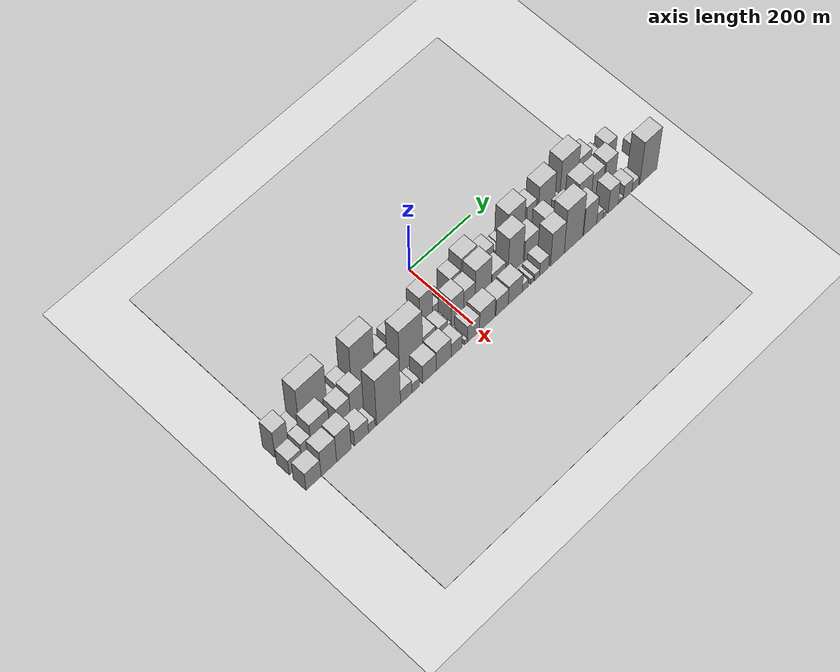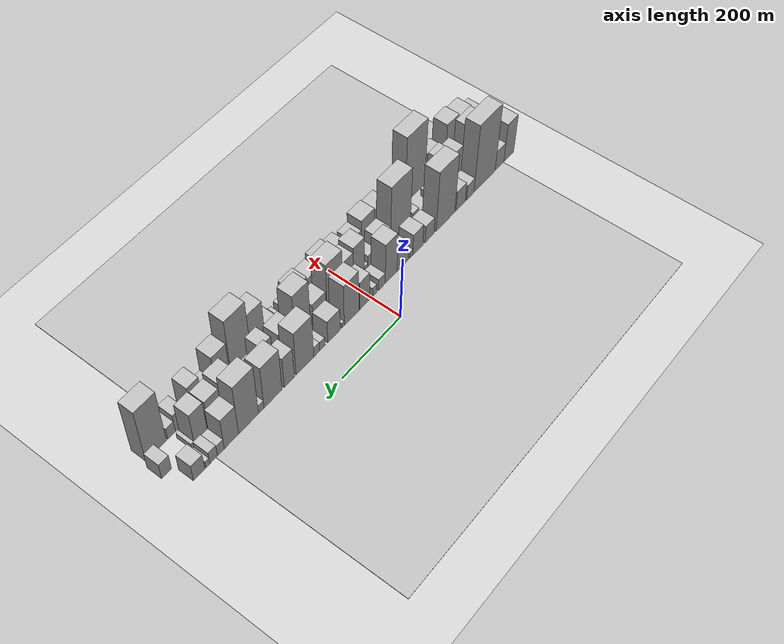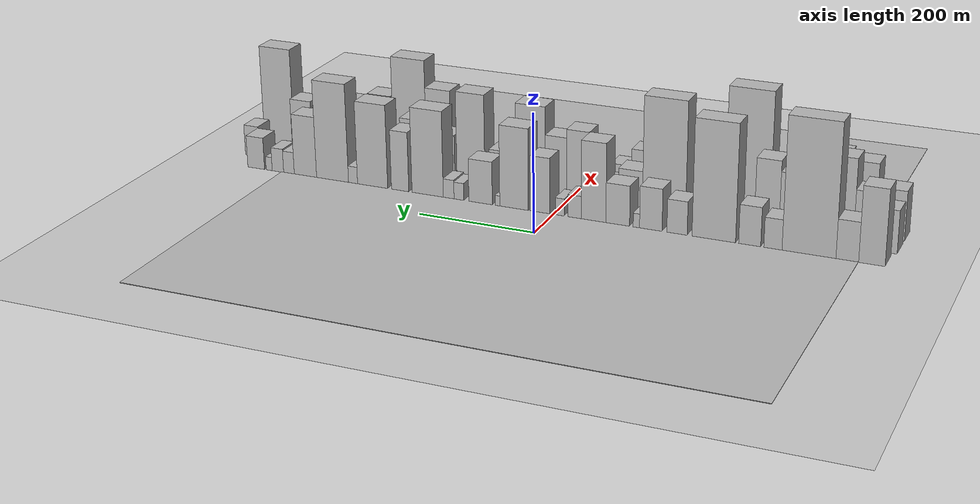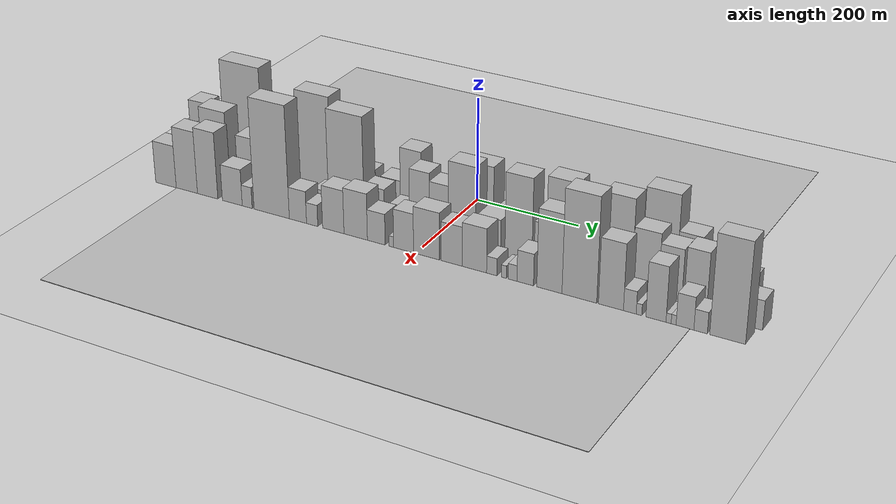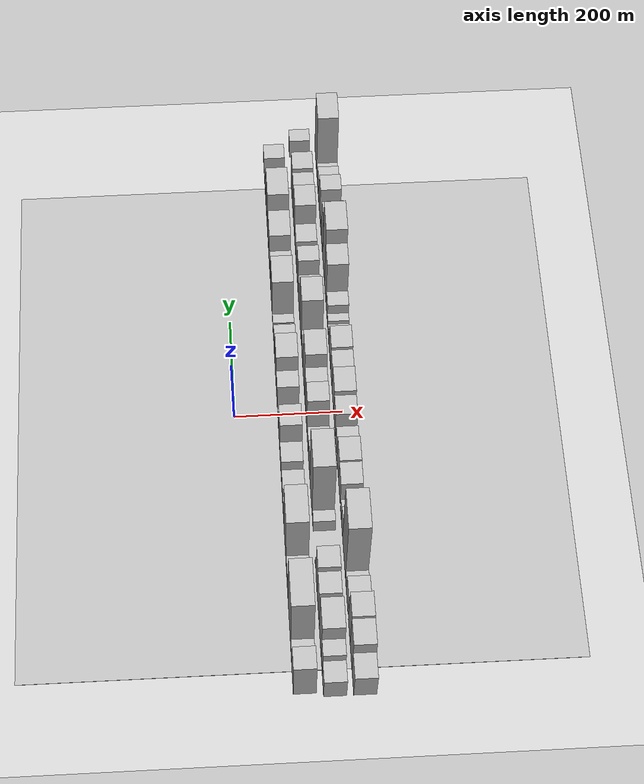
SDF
<?xml version="1.0" encoding="utf-8"?>

<sdf version="1.6">

   <world name="default">

      <gui fullscreen="0">

         <camera name="user_camera">

            <pose>-15 0 4.57585 0 0 0</pose>

            <view_controller>orbit</view_controller>

         </camera>

      </gui>

      <scene>

         <sky>

           <clouds>

             <speed>12</speed>

           </clouds>

         </sky>

         <ambient>0.4 0.4 0.4 1</ambient>

         <background>0.7 0.7 0.7 1</background>

         <shadows>1</shadows>

      </scene>

      <gravity>0 0 -9.8066</gravity>

      <magnetic_field>6e-06 2.3e-05 -4.2e-05</magnetic_field>

      <physics default="0" name="default_physics" type="ode">

         <ode>

            <solver>

               <type>quick</type>

               <iters>10</iters>

               <sor>1.0</sor>

               <use_dynamic_moi_rescaling>0</use_dynamic_moi_rescaling>

            </solver>

            <constraints>

               <cfm>0</cfm>

               <erp>0.2</erp>

               <contact_max_correcting_vel>100</contact_max_correcting_vel>

               <contact_surface_layer>0.001</contact_surface_layer>

            </constraints>

         </ode>

         <max_step_size>0.004</max_step_size>

         <real_time_factor>1</real_time_factor>

         <real_time_update_rate>250</real_time_update_rate>

      </physics>

      <light name="sun" type="directional">

         <cast_shadows>1</cast_shadows>

         <pose>0 0 10 0 0 0</pose>

         <diffuse>0.8 0.8 0.8 1</diffuse>

         <specular>0.2 0.2 0.2 1</specular>

         <attenuation>

            <range>1000</range>

            <constant>0.9</constant>

            <linear>0.01</linear>

            <quadratic>0.001</quadratic>

         </attenuation>

         <direction>-0.5 0.1 -0.9</direction>

      </light>

      <include>

         <name>ground_plane_1</name>

         <uri>model://HANNAS_ground_plane</uri>

         <pose>0 0 0  0 0 0</pose>

      </include>

      <include>

         <name>ground_plane_2</name>

         <uri>model://HANNAS_ground_plane</uri>

         <pose>100 0 0  0 0 0</pose>

      </include>

      <model name="building_1">

         <static>1</static>

         <pose frame="">100.0000 -520.6424 0 0.000000 0.000000 0.000000</pose>

         <link name="link">

            <pose frame="">0 0 63.00 0 0 0</pose>

            <collision name="collision">

               <geometry>

                  <box>

                     <size>40.0000 40.7153 126.0000</size>

                  </box>

               </geometry>

               <max_contacts>10</max_contacts>

               <surface>

                  <contact>

                     <ode/>

                  </contact>

                  <bounce/>

                  <friction>

                     <torsional>

                        <ode/>

                     </torsional>

                     <ode/>

                  </friction>

               </surface>

            </collision>

            <visual name="visual">

               <cast_shadows>0</cast_shadows>

               <geometry>

                  <box>

                     <size>40.0000 40.7153 126.0000</size>

                  </box>

               </geometry>

               <material>

                  <script>

                     <uri>model://HANNAS_wall/materials/scripts</uri>

                     <uri>model://HANNAS_wall/materials/textures</uri>

                     <name>vrc/HANNAS_wall</name>

                  </script>

               </material>

            </visual>

            <self_collide>0</self_collide>

            <enable_wind>0</enable_wind>

            <kinematic>0</kinematic>

         </link>

      </model>

      <model name="building_2">

         <static>1</static>

         <pose frame="">100.0000 -482.6814 0 0.000000 0.000000 0.000000</pose>

         <link name="link">

            <pose frame="">0 0 33.00 0 0 0</pose>

            <collision name="collision">

               <geometry>

                  <box>

                     <size>40.0000 35.2066 66.0000</size>

                  </box>

               </geometry>

               <max_contacts>10</max_contacts>

               <surface>

                  <contact>

                     <ode/>

                  </contact>

                  <bounce/>

                  <friction>

                     <torsional>

                        <ode/>

                     </torsional>

                     <ode/>

                  </friction>

               </surface>

            </collision>

            <visual name="visual">

               <cast_shadows>0</cast_shadows>

               <geometry>

                  <box>

                     <size>40.0000 35.2066 66.0000</size>

                  </box>

               </geometry>

               <material>

                  <script>

                     <uri>model://HANNAS_wall/materials/scripts</uri>

                     <uri>model://HANNAS_wall/materials/textures</uri>

                     <name>vrc/HANNAS_wall</name>

                  </script>

               </material>

            </visual>

            <self_collide>0</self_collide>

            <enable_wind>0</enable_wind>

            <kinematic>0</kinematic>

         </link>

      </model>

      <model name="building_3">

         <static>1</static>

         <pose frame="">100.0000 -422.6108 0 0.000000 0.000000 0.000000</pose>

         <link name="link">

            <pose frame="">0 0 111.00 0 0 0</pose>

            <collision name="collision">

               <geometry>

                  <box>

                     <size>40.0000 84.9346 222.0000</size>

                  </box>

               </geometry>

               <max_contacts>10</max_contacts>

               <surface>

                  <contact>

                     <ode/>

                  </contact>

                  <bounce/>

                  <friction>

                     <torsional>

                        <ode/>

                     </torsional>

                     <ode/>

                  </friction>

               </surface>

            </collision>

            <visual name="visual">

               <cast_shadows>0</cast_shadows>

               <geometry>

                  <box>

                     <size>40.0000 84.9346 222.0000</size>

                  </box>

               </geometry>

               <material>

                  <script>

                     <uri>model://HANNAS_wall/materials/scripts</uri>

                     <uri>model://HANNAS_wall/materials/textures</uri>

                     <name>vrc/HANNAS_wall</name>

                  </script>

               </material>

            </visual>

            <self_collide>0</self_collide>

            <enable_wind>0</enable_wind>

            <kinematic>0</kinematic>

         </link>

      </model>

      <model name="building_4">

         <static>1</static>

         <pose frame="">100.0000 -365.6427 0 0.000000 0.000000 0.000000</pose>

         <link name="link">

            <pose frame="">0 0 25.50 0 0 0</pose>

            <collision name="collision">

               <geometry>

                  <box>

                     <size>40.0000 29.0015 51.0000</size>

                  </box>

               </geometry>

               <max_contacts>10</max_contacts>

               <surface>

                  <contact>

                     <ode/>

                  </contact>

                  <bounce/>

                  <friction>

                     <torsional>

                        <ode/>

                     </torsional>

                     <ode/>

                  </friction>

               </surface>

            </collision>

            <visual name="visual">

               <cast_shadows>0</cast_shadows>

               <geometry>

                  <box>

                     <size>40.0000 29.0015 51.0000</size>

                  </box>

               </geometry>

               <material>

                  <script>

                     <uri>model://HANNAS_wall/materials/scripts</uri>

                     <uri>model://HANNAS_wall/materials/textures</uri>

                     <name>vrc/HANNAS_wall</name>

                  </script>

               </material>

            </visual>

            <self_collide>0</self_collide>

            <enable_wind>0</enable_wind>

            <kinematic>0</kinematic>

         </link>

      </model>

      <model name="building_5">

         <static>1</static>

         <pose frame="">100.0000 -328.3756 0 0.000000 0.000000 0.000000</pose>

         <link name="link">

            <pose frame="">0 0 33.00 0 0 0</pose>

            <collision name="collision">

               <geometry>

                  <box>

                     <size>40.0000 35.5327 66.0000</size>

                  </box>

               </geometry>

               <max_contacts>10</max_contacts>

               <surface>

                  <contact>

                     <ode/>

                  </contact>

                  <bounce/>

                  <friction>

                     <torsional>

                        <ode/>

                     </torsional>

                     <ode/>

                  </friction>

               </surface>

            </collision>

            <visual name="visual">

               <cast_shadows>0</cast_shadows>

               <geometry>

                  <box>

                     <size>40.0000 35.5327 66.0000</size>

                  </box>

               </geometry>

               <material>

                  <script>

                     <uri>model://HANNAS_wall/materials/scripts</uri>

                     <uri>model://HANNAS_wall/materials/textures</uri>

                     <name>vrc/HANNAS_wall</name>

                  </script>

               </material>

            </visual>

            <self_collide>0</self_collide>

            <enable_wind>0</enable_wind>

            <kinematic>0</kinematic>

         </link>

      </model>

      <model name="building_6">

         <static>1</static>

         <pose frame="">100.0000 -270.0460 0 0.000000 0.000000 0.000000</pose>

         <link name="link">

            <pose frame="">0 0 99.00 0 0 0</pose>

            <collision name="collision">

               <geometry>

                  <box>

                     <size>40.0000 71.1264 198.0000</size>

                  </box>

               </geometry>

               <max_contacts>10</max_contacts>

               <surface>

                  <contact>

                     <ode/>

                  </contact>

                  <bounce/>

                  <friction>

                     <torsional>

                        <ode/>

                     </torsional>

                     <ode/>

                  </friction>

               </surface>

            </collision>

            <visual name="visual">

               <cast_shadows>0</cast_shadows>

               <geometry>

                  <box>

                     <size>40.0000 71.1264 198.0000</size>

                  </box>

               </geometry>

               <material>

                  <script>

                     <uri>model://HANNAS_wall/materials/scripts</uri>

                     <uri>model://HANNAS_wall/materials/textures</uri>

                     <name>vrc/HANNAS_wall</name>

                  </script>

               </material>

            </visual>

            <self_collide>0</self_collide>

            <enable_wind>0</enable_wind>

            <kinematic>0</kinematic>

         </link>

      </model>

      <model name="building_7">

         <static>1</static>

         <pose frame="">100.0000 -209.6957 0 0.000000 0.000000 0.000000</pose>

         <link name="link">

            <pose frame="">0 0 28.50 0 0 0</pose>

            <collision name="collision">

               <geometry>

                  <box>

                     <size>40.0000 33.5742 57.0000</size>

                  </box>

               </geometry>

               <max_contacts>10</max_contacts>

               <surface>

                  <contact>

                     <ode/>

                  </contact>

                  <bounce/>

                  <friction>

                     <torsional>

                        <ode/>

                     </torsional>

                     <ode/>

                  </friction>

               </surface>

            </collision>

            <visual name="visual">

               <cast_shadows>0</cast_shadows>

               <geometry>

                  <box>

                     <size>40.0000 33.5742 57.0000</size>

                  </box>

               </geometry>

               <material>

                  <script>

                     <uri>model://HANNAS_wall/materials/scripts</uri>

                     <uri>model://HANNAS_wall/materials/textures</uri>

                     <name>vrc/HANNAS_wall</name>

                  </script>

               </material>

            </visual>

            <self_collide>0</self_collide>

            <enable_wind>0</enable_wind>

            <kinematic>0</kinematic>

         </link>

      </model>

      <model name="building_8">

         <static>1</static>

         <pose frame="">100.0000 -166.0464 0 0.000000 0.000000 0.000000</pose>

         <link name="link">

            <pose frame="">0 0 36.00 0 0 0</pose>

            <collision name="collision">

               <geometry>

                  <box>

                     <size>40.0000 37.7243 72.0000</size>

                  </box>

               </geometry>

               <max_contacts>10</max_contacts>

               <surface>

                  <contact>

                     <ode/>

                  </contact>

                  <bounce/>

                  <friction>

                     <torsional>

                        <ode/>

                     </torsional>

                     <ode/>

                  </friction>

               </surface>

            </collision>

            <visual name="visual">

               <cast_shadows>0</cast_shadows>

               <geometry>

                  <box>

                     <size>40.0000 37.7243 72.0000</size>

                  </box>

               </geometry>

               <material>

                  <script>

                     <uri>model://HANNAS_wall/materials/scripts</uri>

                     <uri>model://HANNAS_wall/materials/textures</uri>

                     <name>vrc/HANNAS_wall</name>

                  </script>

               </material>

            </visual>

            <self_collide>0</self_collide>

            <enable_wind>0</enable_wind>

            <kinematic>0</kinematic>

         </link>

      </model>

      <model name="building_9">

         <static>1</static>

         <pose frame="">100.0000 -141.8162 0 0.000000 0.000000 0.000000</pose>

         <link name="link">

            <pose frame="">0 0 12.00 0 0 0</pose>

            <collision name="collision">

               <geometry>

                  <box>

                     <size>40.0000 10.7360 24.0000</size>

                  </box>

               </geometry>

               <max_contacts>10</max_contacts>

               <surface>

                  <contact>

                     <ode/>

                  </contact>

                  <bounce/>

                  <friction>

                     <torsional>

                        <ode/>

                     </torsional>

                     <ode/>

                  </friction>

               </surface>

            </collision>

            <visual name="visual">

               <cast_shadows>0</cast_shadows>

               <geometry>

                  <box>

                     <size>40.0000 10.7360 24.0000</size>

                  </box>

               </geometry>

               <material>

                  <script>

                     <uri>model://HANNAS_wall/materials/scripts</uri>

                     <uri>model://HANNAS_wall/materials/textures</uri>

                     <name>vrc/HANNAS_wall</name>

                  </script>

               </material>

            </visual>

            <self_collide>0</self_collide>

            <enable_wind>0</enable_wind>

            <kinematic>0</kinematic>

         </link>

      </model>

      <model name="building_10">

         <static>1</static>

         <pose frame="">100.0000 -110.3357 0 0.000000 0.000000 0.000000</pose>

         <link name="link">

            <pose frame="">0 0 34.50 0 0 0</pose>

            <collision name="collision">

               <geometry>

                  <box>

                     <size>40.0000 40.2250 69.0000</size>

                  </box>

               </geometry>

               <max_contacts>10</max_contacts>

               <surface>

                  <contact>

                     <ode/>

                  </contact>

                  <bounce/>

                  <friction>

                     <torsional>

                        <ode/>

                     </torsional>

                     <ode/>

                  </friction>

               </surface>

            </collision>

            <visual name="visual">

               <cast_shadows>0</cast_shadows>

               <geometry>

                  <box>

                     <size>40.0000 40.2250 69.0000</size>

                  </box>

               </geometry>

               <material>

                  <script>

                     <uri>model://HANNAS_wall/materials/scripts</uri>

                     <uri>model://HANNAS_wall/materials/textures</uri>

                     <name>vrc/HANNAS_wall</name>

                  </script>

               </material>

            </visual>

            <self_collide>0</self_collide>

            <enable_wind>0</enable_wind>

            <kinematic>0</kinematic>

         </link>

      </model>

      <model name="building_11">

         <static>1</static>

         <pose frame="">100.0000 -69.0624 0 0.000000 0.000000 0.000000</pose>

         <link name="link">

            <pose frame="">0 0 67.50 0 0 0</pose>

            <collision name="collision">

               <geometry>

                  <box>

                     <size>40.0000 42.3215 135.0000</size>

                  </box>

               </geometry>

               <max_contacts>10</max_contacts>

               <surface>

                  <contact>

                     <ode/>

                  </contact>

                  <bounce/>

                  <friction>

                     <torsional>

                        <ode/>

                     </torsional>

                     <ode/>

                  </friction>

               </surface>

            </collision>

            <visual name="visual">

               <cast_shadows>0</cast_shadows>

               <geometry>

                  <box>

                     <size>40.0000 42.3215 135.0000</size>

                  </box>

               </geometry>

               <material>

                  <script>

                     <uri>model://HANNAS_wall/materials/scripts</uri>

                     <uri>model://HANNAS_wall/materials/textures</uri>

                     <name>vrc/HANNAS_wall</name>

                  </script>

               </material>

            </visual>

            <self_collide>0</self_collide>

            <enable_wind>0</enable_wind>

            <kinematic>0</kinematic>

         </link>

      </model>

      <model name="building_12">

         <static>1</static>

         <pose frame="">100.0000 -36.2904 0 0.000000 0.000000 0.000000</pose>

         <link name="link">

            <pose frame="">0 0 19.50 0 0 0</pose>

            <collision name="collision">

               <geometry>

                  <box>

                     <size>40.0000 23.2225 39.0000</size>

                  </box>

               </geometry>

               <max_contacts>10</max_contacts>

               <surface>

                  <contact>

                     <ode/>

                  </contact>

                  <bounce/>

                  <friction>

                     <torsional>

                        <ode/>

                     </torsional>

                     <ode/>

                  </friction>

               </surface>

            </collision>

            <visual name="visual">

               <cast_shadows>0</cast_shadows>

               <geometry>

                  <box>

                     <size>40.0000 23.2225 39.0000</size>

                  </box>

               </geometry>

               <material>

                  <script>

                     <uri>model://HANNAS_wall/materials/scripts</uri>

                     <uri>model://HANNAS_wall/materials/textures</uri>

                     <name>vrc/HANNAS_wall</name>

                  </script>

               </material>

            </visual>

            <self_collide>0</self_collide>

            <enable_wind>0</enable_wind>

            <kinematic>0</kinematic>

         </link>

      </model>

      <model name="building_13">

         <static>1</static>

         <pose frame="">100.0000 -11.0439 0 0.000000 0.000000 0.000000</pose>

         <link name="link">

            <pose frame="">0 0 15.00 0 0 0</pose>

            <collision name="collision">

               <geometry>

                  <box>

                     <size>40.0000 15.2705 30.0000</size>

                  </box>

               </geometry>

               <max_contacts>10</max_contacts>

               <surface>

                  <contact>

                     <ode/>

                  </contact>

                  <bounce/>

                  <friction>

                     <torsional>

                        <ode/>

                     </torsional>

                     <ode/>

                  </friction>

               </surface>

            </collision>

            <visual name="visual">

               <cast_shadows>0</cast_shadows>

               <geometry>

                  <box>

                     <size>40.0000 15.2705 30.0000</size>

                  </box>

               </geometry>

               <material>

                  <script>

                     <uri>model://HANNAS_wall/materials/scripts</uri>

                     <uri>model://HANNAS_wall/materials/textures</uri>

                     <name>vrc/HANNAS_wall</name>

                  </script>

               </material>

            </visual>

            <self_collide>0</self_collide>

            <enable_wind>0</enable_wind>

            <kinematic>0</kinematic>

         </link>

      </model>

      <model name="building_14">

         <static>1</static>

         <pose frame="">100.0000 23.7268 0 0.000000 0.000000 0.000000</pose>

         <link name="link">

            <pose frame="">0 0 48.00 0 0 0</pose>

            <collision name="collision">

               <geometry>

                  <box>

                     <size>40.0000 34.2709 96.0000</size>

                  </box>

               </geometry>

               <max_contacts>10</max_contacts>

               <surface>

                  <contact>

                     <ode/>

                  </contact>

                  <bounce/>

                  <friction>

                     <torsional>

                        <ode/>

                     </torsional>

                     <ode/>

                  </friction>

               </surface>

            </collision>

            <visual name="visual">

               <cast_shadows>0</cast_shadows>

               <geometry>

                  <box>

                     <size>40.0000 34.2709 96.0000</size>

                  </box>

               </geometry>

               <material>

                  <script>

                     <uri>model://HANNAS_wall/materials/scripts</uri>

                     <uri>model://HANNAS_wall/materials/textures</uri>

                     <name>vrc/HANNAS_wall</name>

                  </script>

               </material>

            </visual>

            <self_collide>0</self_collide>

            <enable_wind>0</enable_wind>

            <kinematic>0</kinematic>

         </link>

      </model>

      <model name="building_15">

         <static>1</static>

         <pose frame="">100.0000 69.0616 0 0.000000 0.000000 0.000000</pose>

         <link name="link">

            <pose frame="">0 0 70.50 0 0 0</pose>

            <collision name="collision">

               <geometry>

                  <box>

                     <size>40.0000 50.3987 141.0000</size>

                  </box>

               </geometry>

               <max_contacts>10</max_contacts>

               <surface>

                  <contact>

                     <ode/>

                  </contact>

                  <bounce/>

                  <friction>

                     <torsional>

                        <ode/>

                     </torsional>

                     <ode/>

                  </friction>

               </surface>

            </collision>

            <visual name="visual">

               <cast_shadows>0</cast_shadows>

               <geometry>

                  <box>

                     <size>40.0000 50.3987 141.0000</size>

                  </box>

               </geometry>

               <material>

                  <script>

                     <uri>model://HANNAS_wall/materials/scripts</uri>

                     <uri>model://HANNAS_wall/materials/textures</uri>

                     <name>vrc/HANNAS_wall</name>

                  </script>

               </material>

            </visual>

            <self_collide>0</self_collide>

            <enable_wind>0</enable_wind>

            <kinematic>0</kinematic>

         </link>

      </model>

      <model name="building_16">

         <static>1</static>

         <pose frame="">100.0000 98.4314 0 0.000000 0.000000 0.000000</pose>

         <link name="link">

            <pose frame="">0 0 9.00 0 0 0</pose>

            <collision name="collision">

               <geometry>

                  <box>

                     <size>40.0000 8.3410 18.0000</size>

                  </box>

               </geometry>

               <max_contacts>10</max_contacts>

               <surface>

                  <contact>

                     <ode/>

                  </contact>

                  <bounce/>

                  <friction>

                     <torsional>

                        <ode/>

                     </torsional>

                     <ode/>

                  </friction>

               </surface>

            </collision>

            <visual name="visual">

               <cast_shadows>0</cast_shadows>

               <geometry>

                  <box>

                     <size>40.0000 8.3410 18.0000</size>

                  </box>

               </geometry>

               <material>

                  <script>

                     <uri>model://HANNAS_wall/materials/scripts</uri>

                     <uri>model://HANNAS_wall/materials/textures</uri>

                     <name>vrc/HANNAS_wall</name>

                  </script>

               </material>

            </visual>

            <self_collide>0</self_collide>

            <enable_wind>0</enable_wind>

            <kinematic>0</kinematic>

         </link>

      </model>

      <model name="building_17">

         <static>1</static>

         <pose frame="">100.0000 128.5890 0 0.000000 0.000000 0.000000</pose>

         <link name="link">

            <pose frame="">0 0 37.50 0 0 0</pose>

            <collision name="collision">

               <geometry>

                  <box>

                     <size>40.0000 41.9741 75.0000</size>

                  </box>

               </geometry>

               <max_contacts>10</max_contacts>

               <surface>

                  <contact>

                     <ode/>

                  </contact>

                  <bounce/>

                  <friction>

                     <torsional>

                        <ode/>

                     </torsional>

                     <ode/>

                  </friction>

               </surface>

            </collision>

            <visual name="visual">

               <cast_shadows>0</cast_shadows>

               <geometry>

                  <box>

                     <size>40.0000 41.9741 75.0000</size>

                  </box>

               </geometry>

               <material>

                  <script>

                     <uri>model://HANNAS_wall/materials/scripts</uri>

                     <uri>model://HANNAS_wall/materials/textures</uri>

                     <name>vrc/HANNAS_wall</name>

                  </script>

               </material>

            </visual>

            <self_collide>0</self_collide>

            <enable_wind>0</enable_wind>

            <kinematic>0</kinematic>

         </link>

      </model>

      <model name="building_18">

         <static>1</static>

         <pose frame="">100.0000 167.4302 0 0.000000 0.000000 0.000000</pose>

         <link name="link">

            <pose frame="">0 0 15.00 0 0 0</pose>

            <collision name="collision">

               <geometry>

                  <box>

                     <size>40.0000 17.7083 30.0000</size>

                  </box>

               </geometry>

               <max_contacts>10</max_contacts>

               <surface>

                  <contact>

                     <ode/>

                  </contact>

                  <bounce/>

                  <friction>

                     <torsional>

                        <ode/>

                     </torsional>

                     <ode/>

                  </friction>

               </surface>

            </collision>

            <visual name="visual">

               <cast_shadows>0</cast_shadows>

               <geometry>

                  <box>

                     <size>40.0000 17.7083 30.0000</size>

                  </box>

               </geometry>

               <material>

                  <script>

                     <uri>model://HANNAS_wall/materials/scripts</uri>

                     <uri>model://HANNAS_wall/materials/textures</uri>

                     <name>vrc/HANNAS_wall</name>

                  </script>

               </material>

            </visual>

            <self_collide>0</self_collide>

            <enable_wind>0</enable_wind>

            <kinematic>0</kinematic>

         </link>

      </model>

      <model name="building_19">

         <static>1</static>

         <pose frame="">100.0000 186.0254 0 0.000000 0.000000 0.000000</pose>

         <link name="link">

            <pose frame="">0 0 16.50 0 0 0</pose>

            <collision name="collision">

               <geometry>

                  <box>

                     <size>40.0000 19.4821 33.0000</size>

                  </box>

               </geometry>

               <max_contacts>10</max_contacts>

               <surface>

                  <contact>

                     <ode/>

                  </contact>

                  <bounce/>

                  <friction>

                     <torsional>

                        <ode/>

                     </torsional>

                     <ode/>

                  </friction>

               </surface>

            </collision>

            <visual name="visual">

               <cast_shadows>0</cast_shadows>

               <geometry>

                  <box>

                     <size>40.0000 19.4821 33.0000</size>

                  </box>

               </geometry>

               <material>

                  <script>

                     <uri>model://HANNAS_wall/materials/scripts</uri>

                     <uri>model://HANNAS_wall/materials/textures</uri>

                     <name>vrc/HANNAS_wall</name>

                  </script>

               </material>

            </visual>

            <self_collide>0</self_collide>

            <enable_wind>0</enable_wind>

            <kinematic>0</kinematic>

         </link>

      </model>

      <model name="building_20">

         <static>1</static>

         <pose frame="">100.0000 224.3693 0 0.000000 0.000000 0.000000</pose>

         <link name="link">

            <pose frame="">0 0 75.00 0 0 0</pose>

            <collision name="collision">

               <geometry>

                  <box>

                     <size>40.0000 57.2055 150.0000</size>

                  </box>

               </geometry>

               <max_contacts>10</max_contacts>

               <surface>

                  <contact>

                     <ode/>

                  </contact>

                  <bounce/>

                  <friction>

                     <torsional>

                        <ode/>

                     </torsional>

                     <ode/>

                  </friction>

               </surface>

            </collision>

            <visual name="visual">

               <cast_shadows>0</cast_shadows>

               <geometry>

                  <box>

                     <size>40.0000 57.2055 150.0000</size>

                  </box>

               </geometry>

               <material>

                  <script>

                     <uri>model://HANNAS_wall/materials/scripts</uri>

                     <uri>model://HANNAS_wall/materials/textures</uri>

                     <name>vrc/HANNAS_wall</name>

                  </script>

               </material>

            </visual>

            <self_collide>0</self_collide>

            <enable_wind>0</enable_wind>

            <kinematic>0</kinematic>

         </link>

      </model>

      <model name="building_21">

         <static>1</static>

         <pose frame="">100.0000 275.0208 0 0.000000 0.000000 0.000000</pose>

         <link name="link">

            <pose frame="">0 0 52.50 0 0 0</pose>

            <collision name="collision">

               <geometry>

                  <box>

                     <size>40.0000 32.0976 105.0000</size>

                  </box>

               </geometry>

               <max_contacts>10</max_contacts>

               <surface>

                  <contact>

                     <ode/>

                  </contact>

                  <bounce/>

                  <friction>

                     <torsional>

                        <ode/>

                     </torsional>

                     <ode/>

                  </friction>

               </surface>

            </collision>

            <visual name="visual">

               <cast_shadows>0</cast_shadows>

               <geometry>

                  <box>

                     <size>40.0000 32.0976 105.0000</size>

                  </box>

               </geometry>

               <material>

                  <script>

                     <uri>model://HANNAS_wall/materials/scripts</uri>

                     <uri>model://HANNAS_wall/materials/textures</uri>

                     <name>vrc/HANNAS_wall</name>

                  </script>

               </material>

            </visual>

            <self_collide>0</self_collide>

            <enable_wind>0</enable_wind>

            <kinematic>0</kinematic>

         </link>

      </model>

      <model name="building_22">

         <static>1</static>

         <pose frame="">100.0000 326.3163 0 0.000000 0.000000 0.000000</pose>

         <link name="link">

            <pose frame="">0 0 73.50 0 0 0</pose>

            <collision name="collision">

               <geometry>

                  <box>

                     <size>40.0000 56.4934 147.0000</size>

                  </box>

               </geometry>

               <max_contacts>10</max_contacts>

               <surface>

                  <contact>

                     <ode/>

                  </contact>

                  <bounce/>

                  <friction>

                     <torsional>

                        <ode/>

                     </torsional>

                     <ode/>

                  </friction>

               </surface>

            </collision>

            <visual name="visual">

               <cast_shadows>0</cast_shadows>

               <geometry>

                  <box>

                     <size>40.0000 56.4934 147.0000</size>

                  </box>

               </geometry>

               <material>

                  <script>

                     <uri>model://HANNAS_wall/materials/scripts</uri>

                     <uri>model://HANNAS_wall/materials/textures</uri>

                     <name>vrc/HANNAS_wall</name>

                  </script>

               </material>

            </visual>

            <self_collide>0</self_collide>

            <enable_wind>0</enable_wind>

            <kinematic>0</kinematic>

         </link>

      </model>

      <model name="building_23">

         <static>1</static>

         <pose frame="">100.0000 363.0550 0 0.000000 0.000000 0.000000</pose>

         <link name="link">

            <pose frame="">0 0 15.00 0 0 0</pose>

            <collision name="collision">

               <geometry>

                  <box>

                     <size>40.0000 16.9841 30.0000</size>

                  </box>

               </geometry>

               <max_contacts>10</max_contacts>

               <surface>

                  <contact>

                     <ode/>

                  </contact>

                  <bounce/>

                  <friction>

                     <torsional>

                        <ode/>

                     </torsional>

                     <ode/>

                  </friction>

               </surface>

            </collision>

            <visual name="visual">

               <cast_shadows>0</cast_shadows>

               <geometry>

                  <box>

                     <size>40.0000 16.9841 30.0000</size>

                  </box>

               </geometry>

               <material>

                  <script>

                     <uri>model://HANNAS_wall/materials/scripts</uri>

                     <uri>model://HANNAS_wall/materials/textures</uri>

                     <name>vrc/HANNAS_wall</name>

                  </script>

               </material>

            </visual>

            <self_collide>0</self_collide>

            <enable_wind>0</enable_wind>

            <kinematic>0</kinematic>

         </link>

      </model>

      <model name="building_24">

         <static>1</static>

         <pose frame="">100.0000 401.9607 0 0.000000 0.000000 0.000000</pose>

         <link name="link">

            <pose frame="">0 0 87.00 0 0 0</pose>

            <collision name="collision">

               <geometry>

                  <box>

                     <size>40.0000 60.8273 174.0000</size>

                  </box>

               </geometry>

               <max_contacts>10</max_contacts>

               <surface>

                  <contact>

                     <ode/>

                  </contact>

                  <bounce/>

                  <friction>

                     <torsional>

                        <ode/>

                     </torsional>

                     <ode/>

                  </friction>

               </surface>

            </collision>

            <visual name="visual">

               <cast_shadows>0</cast_shadows>

               <geometry>

                  <box>

                     <size>40.0000 60.8273 174.0000</size>

                  </box>

               </geometry>

               <material>

                  <script>

                     <uri>model://HANNAS_wall/materials/scripts</uri>

                     <uri>model://HANNAS_wall/materials/textures</uri>

                     <name>vrc/HANNAS_wall</name>

                  </script>

               </material>

            </visual>

            <self_collide>0</self_collide>

            <enable_wind>0</enable_wind>

            <kinematic>0</kinematic>

         </link>

      </model>

      <model name="building_25">

         <static>1</static>

         <pose frame="">100.0000 453.8556 0 0.000000 0.000000 0.000000</pose>

         <link name="link">

            <pose frame="">0 0 54.00 0 0 0</pose>

            <collision name="collision">

               <geometry>

                  <box>

                     <size>40.0000 42.9626 108.0000</size>

                  </box>

               </geometry>

               <max_contacts>10</max_contacts>

               <surface>

                  <contact>

                     <ode/>

                  </contact>

                  <bounce/>

                  <friction>

                     <torsional>

                        <ode/>

                     </torsional>

                     <ode/>

                  </friction>

               </surface>

            </collision>

            <visual name="visual">

               <cast_shadows>0</cast_shadows>

               <geometry>

                  <box>

                     <size>40.0000 42.9626 108.0000</size>

                  </box>

               </geometry>

               <material>

                  <script>

                     <uri>model://HANNAS_wall/materials/scripts</uri>

                     <uri>model://HANNAS_wall/materials/textures</uri>

                     <name>vrc/HANNAS_wall</name>

                  </script>

               </material>

            </visual>

            <self_collide>0</self_collide>

            <enable_wind>0</enable_wind>

            <kinematic>0</kinematic>

         </link>

      </model>

      <model name="building_26">

         <static>1</static>

         <pose frame="">100.0000 485.6503 0 0.000000 0.000000 0.000000</pose>

         <link name="link">

            <pose frame="">0 0 19.50 0 0 0</pose>

            <collision name="collision">

               <geometry>

                  <box>

                     <size>40.0000 20.6268 39.0000</size>

                  </box>

               </geometry>

               <max_contacts>10</max_contacts>

               <surface>

                  <contact>

                     <ode/>

                  </contact>

                  <bounce/>

                  <friction>

                     <torsional>

                        <ode/>

                     </torsional>

                     <ode/>

                  </friction>

               </surface>

            </collision>

            <visual name="visual">

               <cast_shadows>0</cast_shadows>

               <geometry>

                  <box>

                     <size>40.0000 20.6268 39.0000</size>

                  </box>

               </geometry>

               <material>

                  <script>

                     <uri>model://HANNAS_wall/materials/scripts</uri>

                     <uri>model://HANNAS_wall/materials/textures</uri>

                     <name>vrc/HANNAS_wall</name>

                  </script>

               </material>

            </visual>

            <self_collide>0</self_collide>

            <enable_wind>0</enable_wind>

            <kinematic>0</kinematic>

         </link>

      </model>

      <model name="building_27">

         <static>1</static>

         <pose frame="">100.0000 507.1280 0 0.000000 0.000000 0.000000</pose>

         <link name="link">

            <pose frame="">0 0 21.00 0 0 0</pose>

            <collision name="collision">

               <geometry>

                  <box>

                     <size>40.0000 22.3287 42.0000</size>

                  </box>

               </geometry>

               <max_contacts>10</max_contacts>

               <surface>

                  <contact>

                     <ode/>

                  </contact>

                  <bounce/>

                  <friction>

                     <torsional>

                        <ode/>

                     </torsional>

                     <ode/>

                  </friction>

               </surface>

            </collision>

            <visual name="visual">

               <cast_shadows>0</cast_shadows>

               <geometry>

                  <box>

                     <size>40.0000 22.3287 42.0000</size>

                  </box>

               </geometry>

               <material>

                  <script>

                     <uri>model://HANNAS_wall/materials/scripts</uri>

                     <uri>model://HANNAS_wall/materials/textures</uri>

                     <name>vrc/HANNAS_wall</name>

                  </script>

               </material>

            </visual>

            <self_collide>0</self_collide>

            <enable_wind>0</enable_wind>

            <kinematic>0</kinematic>

         </link>

      </model>

      <model name="building_28">

         <static>1</static>

         <pose frame="">100.0000 524.1989 0 0.000000 0.000000 0.000000</pose>

         <link name="link">

            <pose frame="">0 0 12.00 0 0 0</pose>

            <collision name="collision">

               <geometry>

                  <box>

                     <size>40.0000 11.8132 24.0000</size>

                  </box>

               </geometry>

               <max_contacts>10</max_contacts>

               <surface>

                  <contact>

                     <ode/>

                  </contact>

                  <bounce/>

                  <friction>

                     <torsional>

                        <ode/>

                     </torsional>

                     <ode/>

                  </friction>

               </surface>

            </collision>

            <visual name="visual">

               <cast_shadows>0</cast_shadows>

               <geometry>

                  <box>

                     <size>40.0000 11.8132 24.0000</size>

                  </box>

               </geometry>

               <material>

                  <script>

                     <uri>model://HANNAS_wall/materials/scripts</uri>

                     <uri>model://HANNAS_wall/materials/textures</uri>

                     <name>vrc/HANNAS_wall</name>

                  </script>

               </material>

            </visual>

            <self_collide>0</self_collide>

            <enable_wind>0</enable_wind>

            <kinematic>0</kinematic>

         </link>

      </model>

      <model name="building_29">

         <static>1</static>

         <pose frame="">100.0000 549.5464 0 0.000000 0.000000 0.000000</pose>

         <link name="link">

            <pose frame="">0 0 28.50 0 0 0</pose>

            <collision name="collision">

               <geometry>

                  <box>

                     <size>40.0000 32.8817 57.0000</size>

                  </box>

               </geometry>

               <max_contacts>10</max_contacts>

               <surface>

                  <contact>

                     <ode/>

                  </contact>

                  <bounce/>

                  <friction>

                     <torsional>

                        <ode/>

                     </torsional>

                     <ode/>

                  </friction>

               </surface>

            </collision>

            <visual name="visual">

               <cast_shadows>0</cast_shadows>

               <geometry>

                  <box>

                     <size>40.0000 32.8817 57.0000</size>

                  </box>

               </geometry>

               <material>

                  <script>

                     <uri>model://HANNAS_wall/materials/scripts</uri>

                     <uri>model://HANNAS_wall/materials/textures</uri>

                     <name>vrc/HANNAS_wall</name>

                  </script>

               </material>

            </visual>

            <self_collide>0</self_collide>

            <enable_wind>0</enable_wind>

            <kinematic>0</kinematic>

         </link>

      </model>

      <model name="building_30">

         <static>1</static>

         <pose frame="">152.0000 -528.5410 0 0.000000 0.000000 0.000000</pose>

         <link name="link">

            <pose frame="">0 0 36.00 0 0 0</pose>

            <collision name="collision">

               <geometry>

                  <box>

                     <size>40.0000 38.9179 72.0000</size>

                  </box>

               </geometry>

               <max_contacts>10</max_contacts>

               <surface>

                  <contact>

                     <ode/>

                  </contact>

                  <bounce/>

                  <friction>

                     <torsional>

                        <ode/>

                     </torsional>

                     <ode/>

                  </friction>

               </surface>

            </collision>

            <visual name="visual">

               <cast_shadows>0</cast_shadows>

               <geometry>

                  <box>

                     <size>40.0000 38.9179 72.0000</size>

                  </box>

               </geometry>

               <material>

                  <script>

                     <uri>model://HANNAS_wall/materials/scripts</uri>

                     <uri>model://HANNAS_wall/materials/textures</uri>

                     <name>vrc/HANNAS_wall</name>

                  </script>

               </material>

            </visual>

            <self_collide>0</self_collide>

            <enable_wind>0</enable_wind>

            <kinematic>0</kinematic>

         </link>

      </model>

      <model name="building_31">

         <static>1</static>

         <pose frame="">152.0000 -494.0532 0 0.000000 0.000000 0.000000</pose>

         <link name="link">

            <pose frame="">0 0 48.00 0 0 0</pose>

            <collision name="collision">

               <geometry>

                  <box>

                     <size>40.0000 30.0578 96.0000</size>

                  </box>

               </geometry>

               <max_contacts>10</max_contacts>

               <surface>

                  <contact>

                     <ode/>

                  </contact>

                  <bounce/>

                  <friction>

                     <torsional>

                        <ode/>

                     </torsional>

                     <ode/>

                  </friction>

               </surface>

            </collision>

            <visual name="visual">

               <cast_shadows>0</cast_shadows>

               <geometry>

                  <box>

                     <size>40.0000 30.0578 96.0000</size>

                  </box>

               </geometry>

               <material>

                  <script>

                     <uri>model://HANNAS_wall/materials/scripts</uri>

                     <uri>model://HANNAS_wall/materials/textures</uri>

                     <name>vrc/HANNAS_wall</name>

                  </script>

               </material>

            </visual>

            <self_collide>0</self_collide>

            <enable_wind>0</enable_wind>

            <kinematic>0</kinematic>

         </link>

      </model>

      <model name="building_32">

         <static>1</static>

         <pose frame="">152.0000 -450.6741 0 0.000000 0.000000 0.000000</pose>

         <link name="link">

            <pose frame="">0 0 73.50 0 0 0</pose>

            <collision name="collision">

               <geometry>

                  <box>

                     <size>40.0000 56.7006 147.0000</size>

                  </box>

               </geometry>

               <max_contacts>10</max_contacts>

               <surface>

                  <contact>

                     <ode/>

                  </contact>

                  <bounce/>

                  <friction>

                     <torsional>

                        <ode/>

                     </torsional>

                     <ode/>

                  </friction>

               </surface>

            </collision>

            <visual name="visual">

               <cast_shadows>0</cast_shadows>

               <geometry>

                  <box>

                     <size>40.0000 56.7006 147.0000</size>

                  </box>

               </geometry>

               <material>

                  <script>

                     <uri>model://HANNAS_wall/materials/scripts</uri>

                     <uri>model://HANNAS_wall/materials/textures</uri>

                     <name>vrc/HANNAS_wall</name>

                  </script>

               </material>

            </visual>

            <self_collide>0</self_collide>

            <enable_wind>0</enable_wind>

            <kinematic>0</kinematic>

         </link>

      </model>

      <model name="building_33">

         <static>1</static>

         <pose frame="">152.0000 -417.8523 0 0.000000 0.000000 0.000000</pose>

         <link name="link">

            <pose frame="">0 0 9.00 0 0 0</pose>

            <collision name="collision">

               <geometry>

                  <box>

                     <size>40.0000 8.9429 18.0000</size>

                  </box>

               </geometry>

               <max_contacts>10</max_contacts>

               <surface>

                  <contact>

                     <ode/>

                  </contact>

                  <bounce/>

                  <friction>

                     <torsional>

                        <ode/>

                     </torsional>

                     <ode/>

                  </friction>

               </surface>

            </collision>

            <visual name="visual">

               <cast_shadows>0</cast_shadows>

               <geometry>

                  <box>

                     <size>40.0000 8.9429 18.0000</size>

                  </box>

               </geometry>

               <material>

                  <script>

                     <uri>model://HANNAS_wall/materials/scripts</uri>

                     <uri>model://HANNAS_wall/materials/textures</uri>

                     <name>vrc/HANNAS_wall</name>

                  </script>

               </material>

            </visual>

            <self_collide>0</self_collide>

            <enable_wind>0</enable_wind>

            <kinematic>0</kinematic>

         </link>

      </model>

      <model name="building_34">

         <static>1</static>

         <pose frame="">152.0000 -407.1909 0 0.000000 0.000000 0.000000</pose>

         <link name="link">

            <pose frame="">0 0 13.50 0 0 0</pose>

            <collision name="collision">

               <geometry>

                  <box>

                     <size>40.0000 12.3799 27.0000</size>

                  </box>

               </geometry>

               <max_contacts>10</max_contacts>

               <surface>

                  <contact>

                     <ode/>

                  </contact>

                  <bounce/>

                  <friction>

                     <torsional>

                        <ode/>

                     </torsional>

                     <ode/>

                  </friction>

               </surface>

            </collision>

            <visual name="visual">

               <cast_shadows>0</cast_shadows>

               <geometry>

                  <box>

                     <size>40.0000 12.3799 27.0000</size>

                  </box>

               </geometry>

               <material>

                  <script>

                     <uri>model://HANNAS_wall/materials/scripts</uri>

                     <uri>model://HANNAS_wall/materials/textures</uri>

                     <name>vrc/HANNAS_wall</name>

                  </script>

               </material>

            </visual>

            <self_collide>0</self_collide>

            <enable_wind>0</enable_wind>

            <kinematic>0</kinematic>

         </link>

      </model>

      <model name="building_35">

         <static>1</static>

         <pose frame="">152.0000 -380.6003 0 0.000000 0.000000 0.000000</pose>

         <link name="link">

            <pose frame="">0 0 54.00 0 0 0</pose>

            <collision name="collision">

               <geometry>

                  <box>

                     <size>40.0000 40.8014 108.0000</size>

                  </box>

               </geometry>

               <max_contacts>10</max_contacts>

               <surface>

                  <contact>

                     <ode/>

                  </contact>

                  <bounce/>

                  <friction>

                     <torsional>

                        <ode/>

                     </torsional>

                     <ode/>

                  </friction>

               </surface>

            </collision>

            <visual name="visual">

               <cast_shadows>0</cast_shadows>

               <geometry>

                  <box>

                     <size>40.0000 40.8014 108.0000</size>

                  </box>

               </geometry>

               <material>

                  <script>

                     <uri>model://HANNAS_wall/materials/scripts</uri>

                     <uri>model://HANNAS_wall/materials/textures</uri>

                     <name>vrc/HANNAS_wall</name>

                  </script>

               </material>

            </visual>

            <self_collide>0</self_collide>

            <enable_wind>0</enable_wind>

            <kinematic>0</kinematic>

         </link>

      </model>

      <model name="building_36">

         <static>1</static>

         <pose frame="">152.0000 -340.1118 0 0.000000 0.000000 0.000000</pose>

         <link name="link">

            <pose frame="">0 0 63.00 0 0 0</pose>

            <collision name="collision">

               <geometry>

                  <box>

                     <size>40.0000 40.1756 126.0000</size>

                  </box>

               </geometry>

               <max_contacts>10</max_contacts>

               <surface>

                  <contact>

                     <ode/>

                  </contact>

                  <bounce/>

                  <friction>

                     <torsional>

                        <ode/>

                     </torsional>

                     <ode/>

                  </friction>

               </surface>

            </collision>

            <visual name="visual">

               <cast_shadows>0</cast_shadows>

               <geometry>

                  <box>

                     <size>40.0000 40.1756 126.0000</size>

                  </box>

               </geometry>

               <material>

                  <script>

                     <uri>model://HANNAS_wall/materials/scripts</uri>

                     <uri>model://HANNAS_wall/materials/textures</uri>

                     <name>vrc/HANNAS_wall</name>

                  </script>

               </material>

            </visual>

            <self_collide>0</self_collide>

            <enable_wind>0</enable_wind>

            <kinematic>0</kinematic>

         </link>

      </model>

      <model name="building_37">

         <static>1</static>

         <pose frame="">152.0000 -304.2109 0 0.000000 0.000000 0.000000</pose>

         <link name="link">

            <pose frame="">0 0 12.00 0 0 0</pose>

            <collision name="collision">

               <geometry>

                  <box>

                     <size>40.0000 11.6261 24.0000</size>

                  </box>

               </geometry>

               <max_contacts>10</max_contacts>

               <surface>

                  <contact>

                     <ode/>

                  </contact>

                  <bounce/>

                  <friction>

                     <torsional>

                        <ode/>

                     </torsional>

                     <ode/>

                  </friction>

               </surface>

            </collision>

            <visual name="visual">

               <cast_shadows>0</cast_shadows>

               <geometry>

                  <box>

                     <size>40.0000 11.6261 24.0000</size>

                  </box>

               </geometry>

               <material>

                  <script>

                     <uri>model://HANNAS_wall/materials/scripts</uri>

                     <uri>model://HANNAS_wall/materials/textures</uri>

                     <name>vrc/HANNAS_wall</name>

                  </script>

               </material>

            </visual>

            <self_collide>0</self_collide>

            <enable_wind>0</enable_wind>

            <kinematic>0</kinematic>

         </link>

      </model>

      <model name="building_38">

         <static>1</static>

         <pose frame="">152.0000 -226.7665 0 0.000000 0.000000 0.000000</pose>

         <link name="link">

            <pose frame="">0 0 21.00 0 0 0</pose>

            <collision name="collision">

               <geometry>

                  <box>

                     <size>40.0000 22.4209 42.0000</size>

                  </box>

               </geometry>

               <max_contacts>10</max_contacts>

               <surface>

                  <contact>

                     <ode/>

                  </contact>

                  <bounce/>

                  <friction>

                     <torsional>

                        <ode/>

                     </torsional>

                     <ode/>

                  </friction>

               </surface>

            </collision>

            <visual name="visual">

               <cast_shadows>0</cast_shadows>

               <geometry>

                  <box>

                     <size>40.0000 22.4209 42.0000</size>

                  </box>

               </geometry>

               <material>

                  <script>

                     <uri>model://HANNAS_wall/materials/scripts</uri>

                     <uri>model://HANNAS_wall/materials/textures</uri>

                     <name>vrc/HANNAS_wall</name>

                  </script>

               </material>

            </visual>

            <self_collide>0</self_collide>

            <enable_wind>0</enable_wind>

            <kinematic>0</kinematic>

         </link>

      </model>

      <model name="building_39">

         <static>1</static>

         <pose frame="">152.0000 -170.0269 0 0.000000 0.000000 0.000000</pose>

         <link name="link">

            <pose frame="">0 0 102.00 0 0 0</pose>

            <collision name="collision">

               <geometry>

                  <box>

                     <size>40.0000 73.0582 204.0000</size>

                  </box>

               </geometry>

               <max_contacts>10</max_contacts>

               <surface>

                  <contact>

                     <ode/>

                  </contact>

                  <bounce/>

                  <friction>

                     <torsional>

                        <ode/>

                     </torsional>

                     <ode/>

                  </friction>

               </surface>

            </collision>

            <visual name="visual">

               <cast_shadows>0</cast_shadows>

               <geometry>

                  <box>

                     <size>40.0000 73.0582 204.0000</size>

                  </box>

               </geometry>

               <material>

                  <script>

                     <uri>model://HANNAS_wall/materials/scripts</uri>

                     <uri>model://HANNAS_wall/materials/textures</uri>

                     <name>vrc/HANNAS_wall</name>

                  </script>

               </material>

            </visual>

            <self_collide>0</self_collide>

            <enable_wind>0</enable_wind>

            <kinematic>0</kinematic>

         </link>

      </model>

      <model name="building_40">

         <static>1</static>

         <pose frame="">152.0000 -112.7403 0 0.000000 0.000000 0.000000</pose>

         <link name="link">

            <pose frame="">0 0 37.50 0 0 0</pose>

            <collision name="collision">

               <geometry>

                  <box>

                     <size>40.0000 41.5151 75.0000</size>

                  </box>

               </geometry>

               <max_contacts>10</max_contacts>

               <surface>

                  <contact>

                     <ode/>

                  </contact>

                  <bounce/>

                  <friction>

                     <torsional>

                        <ode/>

                     </torsional>

                     <ode/>

                  </friction>

               </surface>

            </collision>

            <visual name="visual">

               <cast_shadows>0</cast_shadows>

               <geometry>

                  <box>

                     <size>40.0000 41.5151 75.0000</size>

                  </box>

               </geometry>

               <material>

                  <script>

                     <uri>model://HANNAS_wall/materials/scripts</uri>

                     <uri>model://HANNAS_wall/materials/textures</uri>

                     <name>vrc/HANNAS_wall</name>

                  </script>

               </material>

            </visual>

            <self_collide>0</self_collide>

            <enable_wind>0</enable_wind>

            <kinematic>0</kinematic>

         </link>

      </model>

      <model name="building_41">

         <static>1</static>

         <pose frame="">152.0000 -67.6886 0 0.000000 0.000000 0.000000</pose>

         <link name="link">

            <pose frame="">0 0 25.50 0 0 0</pose>

            <collision name="collision">

               <geometry>

                  <box>

                     <size>40.0000 28.5882 51.0000</size>

                  </box>

               </geometry>

               <max_contacts>10</max_contacts>

               <surface>

                  <contact>

                     <ode/>

                  </contact>

                  <bounce/>

                  <friction>

                     <torsional>

                        <ode/>

                     </torsional>

                     <ode/>

                  </friction>

               </surface>

            </collision>

            <visual name="visual">

               <cast_shadows>0</cast_shadows>

               <geometry>

                  <box>

                     <size>40.0000 28.5882 51.0000</size>

                  </box>

               </geometry>

               <material>

                  <script>

                     <uri>model://HANNAS_wall/materials/scripts</uri>

                     <uri>model://HANNAS_wall/materials/textures</uri>

                     <name>vrc/HANNAS_wall</name>

                  </script>

               </material>

            </visual>

            <self_collide>0</self_collide>

            <enable_wind>0</enable_wind>

            <kinematic>0</kinematic>

         </link>

      </model>

      <model name="building_42">

         <static>1</static>

         <pose frame="">152.0000 -47.5495 0 0.000000 0.000000 0.000000</pose>

         <link name="link">

            <pose frame="">0 0 13.50 0 0 0</pose>

            <collision name="collision">

               <geometry>

                  <box>

                     <size>40.0000 11.6902 27.0000</size>

                  </box>

               </geometry>

               <max_contacts>10</max_contacts>

               <surface>

                  <contact>

                     <ode/>

                  </contact>

                  <bounce/>

                  <friction>

                     <torsional>

                        <ode/>

                     </torsional>

                     <ode/>

                  </friction>

               </surface>

            </collision>

            <visual name="visual">

               <cast_shadows>0</cast_shadows>

               <geometry>

                  <box>

                     <size>40.0000 11.6902 27.0000</size>

                  </box>

               </geometry>

               <material>

                  <script>

                     <uri>model://HANNAS_wall/materials/scripts</uri>

                     <uri>model://HANNAS_wall/materials/textures</uri>

                     <name>vrc/HANNAS_wall</name>

                  </script>

               </material>

            </visual>

            <self_collide>0</self_collide>

            <enable_wind>0</enable_wind>

            <kinematic>0</kinematic>

         </link>

      </model>

      <model name="building_43">

         <static>1</static>

         <pose frame="">152.0000 -21.8932 0 0.000000 0.000000 0.000000</pose>

         <link name="link">

            <pose frame="">0 0 64.50 0 0 0</pose>

            <collision name="collision">

               <geometry>

                  <box>

                     <size>40.0000 39.6225 129.0000</size>

                  </box>

               </geometry>

               <max_contacts>10</max_contacts>

               <surface>

                  <contact>

                     <ode/>

                  </contact>

                  <bounce/>

                  <friction>

                     <torsional>

                        <ode/>

                     </torsional>

                     <ode/>

                  </friction>

               </surface>

            </collision>

            <visual name="visual">

               <cast_shadows>0</cast_shadows>

               <geometry>

                  <box>

                     <size>40.0000 39.6225 129.0000</size>

                  </box>

               </geometry>

               <material>

                  <script>

                     <uri>model://HANNAS_wall/materials/scripts</uri>

                     <uri>model://HANNAS_wall/materials/textures</uri>

                     <name>vrc/HANNAS_wall</name>

                  </script>

               </material>

            </visual>

            <self_collide>0</self_collide>

            <enable_wind>0</enable_wind>

            <kinematic>0</kinematic>

         </link>

      </model>

      <model name="building_44">

         <static>1</static>

         <pose frame="">152.0000 16.5886 0 0.000000 0.000000 0.000000</pose>

         <link name="link">

            <pose frame="">0 0 57.00 0 0 0</pose>

            <collision name="collision">

               <geometry>

                  <box>

                     <size>40.0000 37.3410 114.0000</size>

                  </box>

               </geometry>

               <max_contacts>10</max_contacts>

               <surface>

                  <contact>

                     <ode/>

                  </contact>

                  <bounce/>

                  <friction>

                     <torsional>

                        <ode/>

                     </torsional>

                     <ode/>

                  </friction>

               </surface>

            </collision>

            <visual name="visual">

               <cast_shadows>0</cast_shadows>

               <geometry>

                  <box>

                     <size>40.0000 37.3410 114.0000</size>

                  </box>

               </geometry>

               <material>

                  <script>

                     <uri>model://HANNAS_wall/materials/scripts</uri>

                     <uri>model://HANNAS_wall/materials/textures</uri>

                     <name>vrc/HANNAS_wall</name>

                  </script>

               </material>

            </visual>

            <self_collide>0</self_collide>

            <enable_wind>0</enable_wind>

            <kinematic>0</kinematic>

         </link>

      </model>

      <model name="building_45">

         <static>1</static>

         <pose frame="">152.0000 61.5552 0 0.000000 0.000000 0.000000</pose>

         <link name="link">

            <pose frame="">0 0 81.00 0 0 0</pose>

            <collision name="collision">

               <geometry>

                  <box>

                     <size>40.0000 52.5924 162.0000</size>

                  </box>

               </geometry>

               <max_contacts>10</max_contacts>

               <surface>

                  <contact>

                     <ode/>

                  </contact>

                  <bounce/>

                  <friction>

                     <torsional>

                        <ode/>

                     </torsional>

                     <ode/>

                  </friction>

               </surface>

            </collision>

            <visual name="visual">

               <cast_shadows>0</cast_shadows>

               <geometry>

                  <box>

                     <size>40.0000 52.5924 162.0000</size>

                  </box>

               </geometry>

               <material>

                  <script>

                     <uri>model://HANNAS_wall/materials/scripts</uri>

                     <uri>model://HANNAS_wall/materials/textures</uri>

                     <name>vrc/HANNAS_wall</name>

                  </script>

               </material>

            </visual>

            <self_collide>0</self_collide>

            <enable_wind>0</enable_wind>

            <kinematic>0</kinematic>

         </link>

      </model>

      <model name="building_46">

         <static>1</static>

         <pose frame="">152.0000 113.2397 0 0.000000 0.000000 0.000000</pose>

         <link name="link">

            <pose frame="">0 0 37.50 0 0 0</pose>

            <collision name="collision">

               <geometry>

                  <box>

                     <size>40.0000 44.7766 75.0000</size>

                  </box>

               </geometry>

               <max_contacts>10</max_contacts>

               <surface>

                  <contact>

                     <ode/>

                  </contact>

                  <bounce/>

                  <friction>

                     <torsional>

                        <ode/>

                     </torsional>

                     <ode/>

                  </friction>

               </surface>

            </collision>

            <visual name="visual">

               <cast_shadows>0</cast_shadows>

               <geometry>

                  <box>

                     <size>40.0000 44.7766 75.0000</size>

                  </box>

               </geometry>

               <material>

                  <script>

                     <uri>model://HANNAS_wall/materials/scripts</uri>

                     <uri>model://HANNAS_wall/materials/textures</uri>

                     <name>vrc/HANNAS_wall</name>

                  </script>

               </material>

            </visual>

            <self_collide>0</self_collide>

            <enable_wind>0</enable_wind>

            <kinematic>0</kinematic>

         </link>

      </model>

      <model name="building_47">

         <static>1</static>

         <pose frame="">152.0000 169.0955 0 0.000000 0.000000 0.000000</pose>

         <link name="link">

            <pose frame="">0 0 84.00 0 0 0</pose>

            <collision name="collision">

               <geometry>

                  <box>

                     <size>40.0000 50.9350 168.0000</size>

                  </box>

               </geometry>

               <max_contacts>10</max_contacts>

               <surface>

                  <contact>

                     <ode/>

                  </contact>

                  <bounce/>

                  <friction>

                     <torsional>

                        <ode/>

                     </torsional>

                     <ode/>

                  </friction>

               </surface>

            </collision>

            <visual name="visual">

               <cast_shadows>0</cast_shadows>

               <geometry>

                  <box>

                     <size>40.0000 50.9350 168.0000</size>

                  </box>

               </geometry>

               <material>

                  <script>

                     <uri>model://HANNAS_wall/materials/scripts</uri>

                     <uri>model://HANNAS_wall/materials/textures</uri>

                     <name>vrc/HANNAS_wall</name>

                  </script>

               </material>

            </visual>

            <self_collide>0</self_collide>

            <enable_wind>0</enable_wind>

            <kinematic>0</kinematic>

         </link>

      </model>

      <model name="building_48">

         <static>1</static>

         <pose frame="">152.0000 221.7921 0 0.000000 0.000000 0.000000</pose>

         <link name="link">

            <pose frame="">0 0 45.00 0 0 0</pose>

            <collision name="collision">

               <geometry>

                  <box>

                     <size>40.0000 46.4581 90.0000</size>

                  </box>

               </geometry>

               <max_contacts>10</max_contacts>

               <surface>

                  <contact>

                     <ode/>

                  </contact>

                  <bounce/>

                  <friction>

                     <torsional>

                        <ode/>

                     </torsional>

                     <ode/>

                  </friction>

               </surface>

            </collision>

            <visual name="visual">

               <cast_shadows>0</cast_shadows>

               <geometry>

                  <box>

                     <size>40.0000 46.4581 90.0000</size>

                  </box>

               </geometry>

               <material>

                  <script>

                     <uri>model://HANNAS_wall/materials/scripts</uri>

                     <uri>model://HANNAS_wall/materials/textures</uri>

                     <name>vrc/HANNAS_wall</name>

                  </script>

               </material>

            </visual>

            <self_collide>0</self_collide>

            <enable_wind>0</enable_wind>

            <kinematic>0</kinematic>

         </link>

      </model>

      <model name="building_49">

         <static>1</static>

         <pose frame="">152.0000 254.8681 0 0.000000 0.000000 0.000000</pose>

         <link name="link">

            <pose frame="">0 0 19.50 0 0 0</pose>

            <collision name="collision">

               <geometry>

                  <box>

                     <size>40.0000 19.6941 39.0000</size>

                  </box>

               </geometry>

               <max_contacts>10</max_contacts>

               <surface>

                  <contact>

                     <ode/>

                  </contact>

                  <bounce/>

                  <friction>

                     <torsional>

                        <ode/>

                     </torsional>

                     <ode/>

                  </friction>

               </surface>

            </collision>

            <visual name="visual">

               <cast_shadows>0</cast_shadows>

               <geometry>

                  <box>

                     <size>40.0000 19.6941 39.0000</size>

                  </box>

               </geometry>

               <material>

                  <script>

                     <uri>model://HANNAS_wall/materials/scripts</uri>

                     <uri>model://HANNAS_wall/materials/textures</uri>

                     <name>vrc/HANNAS_wall</name>

                  </script>

               </material>

            </visual>

            <self_collide>0</self_collide>

            <enable_wind>0</enable_wind>

            <kinematic>0</kinematic>

         </link>

      </model>

      <model name="building_50">

         <static>1</static>

         <pose frame="">152.0000 281.5579 0 0.000000 0.000000 0.000000</pose>

         <link name="link">

            <pose frame="">0 0 54.00 0 0 0</pose>

            <collision name="collision">

               <geometry>

                  <box>

                     <size>40.0000 33.6855 108.0000</size>

                  </box>

               </geometry>

               <max_contacts>10</max_contacts>

               <surface>

                  <contact>

                     <ode/>

                  </contact>

                  <bounce/>

                  <friction>

                     <torsional>

                        <ode/>

                     </torsional>

                     <ode/>

                  </friction>

               </surface>

            </collision>

            <visual name="visual">

               <cast_shadows>0</cast_shadows>

               <geometry>

                  <box>

                     <size>40.0000 33.6855 108.0000</size>

                  </box>

               </geometry>

               <material>

                  <script>

                     <uri>model://HANNAS_wall/materials/scripts</uri>

                     <uri>model://HANNAS_wall/materials/textures</uri>

                     <name>vrc/HANNAS_wall</name>

                  </script>

               </material>

            </visual>

            <self_collide>0</self_collide>

            <enable_wind>0</enable_wind>

            <kinematic>0</kinematic>

         </link>

      </model>

      <model name="building_51">

         <static>1</static>

         <pose frame="">152.0000 312.1706 0 0.000000 0.000000 0.000000</pose>

         <link name="link">

            <pose frame="">0 0 24.00 0 0 0</pose>

            <collision name="collision">

               <geometry>

                  <box>

                     <size>40.0000 27.5398 48.0000</size>

                  </box>

               </geometry>

               <max_contacts>10</max_contacts>

               <surface>

                  <contact>

                     <ode/>

                  </contact>

                  <bounce/>

                  <friction>

                     <torsional>

                        <ode/>

                     </torsional>

                     <ode/>

                  </friction>

               </surface>

            </collision>

            <visual name="visual">

               <cast_shadows>0</cast_shadows>

               <geometry>

                  <box>

                     <size>40.0000 27.5398 48.0000</size>

                  </box>

               </geometry>

               <material>

                  <script>

                     <uri>model://HANNAS_wall/materials/scripts</uri>

                     <uri>model://HANNAS_wall/materials/textures</uri>

                     <name>vrc/HANNAS_wall</name>

                  </script>

               </material>

            </visual>

            <self_collide>0</self_collide>

            <enable_wind>0</enable_wind>

            <kinematic>0</kinematic>

         </link>

      </model>

      <model name="building_52">

         <static>1</static>

         <pose frame="">152.0000 349.2109 0 0.000000 0.000000 0.000000</pose>

         <link name="link">

            <pose frame="">0 0 36.00 0 0 0</pose>

            <collision name="collision">

               <geometry>

                  <box>

                     <size>40.0000 40.5409 72.0000</size>

                  </box>

               </geometry>

               <max_contacts>10</max_contacts>

               <surface>

                  <contact>

                     <ode/>

                  </contact>

                  <bounce/>

                  <friction>

                     <torsional>

                        <ode/>

                     </torsional>

                     <ode/>

                  </friction>

               </surface>

            </collision>

            <visual name="visual">

               <cast_shadows>0</cast_shadows>

               <geometry>

                  <box>

                     <size>40.0000 40.5409 72.0000</size>

                  </box>

               </geometry>

               <material>

                  <script>

                     <uri>model://HANNAS_wall/materials/scripts</uri>

                     <uri>model://HANNAS_wall/materials/textures</uri>

                     <name>vrc/HANNAS_wall</name>

                  </script>

               </material>

            </visual>

            <self_collide>0</self_collide>

            <enable_wind>0</enable_wind>

            <kinematic>0</kinematic>

         </link>

      </model>

      <model name="building_53">

         <static>1</static>

         <pose frame="">152.0000 372.8206 0 0.000000 0.000000 0.000000</pose>

         <link name="link">

            <pose frame="">0 0 7.50 0 0 0</pose>

            <collision name="collision">

               <geometry>

                  <box>

                     <size>40.0000 6.6785 15.0000</size>

                  </box>

               </geometry>

               <max_contacts>10</max_contacts>

               <surface>

                  <contact>

                     <ode/>

                  </contact>

                  <bounce/>

                  <friction>

                     <torsional>

                        <ode/>

                     </torsional>

                     <ode/>

                  </friction>

               </surface>

            </collision>

            <visual name="visual">

               <cast_shadows>0</cast_shadows>

               <geometry>

                  <box>

                     <size>40.0000 6.6785 15.0000</size>

                  </box>

               </geometry>

               <material>

                  <script>

                     <uri>model://HANNAS_wall/materials/scripts</uri>

                     <uri>model://HANNAS_wall/materials/textures</uri>

                     <name>vrc/HANNAS_wall</name>

                  </script>

               </material>

            </visual>

            <self_collide>0</self_collide>

            <enable_wind>0</enable_wind>

            <kinematic>0</kinematic>

         </link>

      </model>

      <model name="building_54">

         <static>1</static>

         <pose frame="">152.0000 399.4634 0 0.000000 0.000000 0.000000</pose>

         <link name="link">

            <pose frame="">0 0 63.00 0 0 0</pose>

            <collision name="collision">

               <geometry>

                  <box>

                     <size>40.0000 46.6072 126.0000</size>

                  </box>

               </geometry>

               <max_contacts>10</max_contacts>

               <surface>

                  <contact>

                     <ode/>

                  </contact>

                  <bounce/>

                  <friction>

                     <torsional>

                        <ode/>

                     </torsional>

                     <ode/>

                  </friction>

               </surface>

            </collision>

            <visual name="visual">

               <cast_shadows>0</cast_shadows>

               <geometry>

                  <box>

                     <size>40.0000 46.6072 126.0000</size>

                  </box>

               </geometry>

               <material>

                  <script>

                     <uri>model://HANNAS_wall/materials/scripts</uri>

                     <uri>model://HANNAS_wall/materials/textures</uri>

                     <name>vrc/HANNAS_wall</name>

                  </script>

               </material>

            </visual>

            <self_collide>0</self_collide>

            <enable_wind>0</enable_wind>

            <kinematic>0</kinematic>

         </link>

      </model>

      <model name="building_55">

         <static>1</static>

         <pose frame="">152.0000 443.1474 0 0.000000 0.000000 0.000000</pose>

         <link name="link">

            <pose frame="">0 0 54.00 0 0 0</pose>

            <collision name="collision">

               <geometry>

                  <box>

                     <size>40.0000 40.7608 108.0000</size>

                  </box>

               </geometry>

               <max_contacts>10</max_contacts>

               <surface>

                  <contact>

                     <ode/>

                  </contact>

                  <bounce/>

                  <friction>

                     <torsional>

                        <ode/>

                     </torsional>

                     <ode/>

                  </friction>

               </surface>

            </collision>

            <visual name="visual">

               <cast_shadows>0</cast_shadows>

               <geometry>

                  <box>

                     <size>40.0000 40.7608 108.0000</size>

                  </box>

               </geometry>

               <material>

                  <script>

                     <uri>model://HANNAS_wall/materials/scripts</uri>

                     <uri>model://HANNAS_wall/materials/textures</uri>

                     <name>vrc/HANNAS_wall</name>

                  </script>

               </material>

            </visual>

            <self_collide>0</self_collide>

            <enable_wind>0</enable_wind>

            <kinematic>0</kinematic>

         </link>

      </model>

      <model name="building_56">

         <static>1</static>

         <pose frame="">152.0000 487.0982 0 0.000000 0.000000 0.000000</pose>

         <link name="link">

            <pose frame="">0 0 57.00 0 0 0</pose>

            <collision name="collision">

               <geometry>

                  <box>

                     <size>40.0000 39.1408 114.0000</size>

                  </box>

               </geometry>

               <max_contacts>10</max_contacts>

               <surface>

                  <contact>

                     <ode/>

                  </contact>

                  <bounce/>

                  <friction>

                     <torsional>

                        <ode/>

                     </torsional>

                     <ode/>

                  </friction>

               </surface>

            </collision>

            <visual name="visual">

               <cast_shadows>0</cast_shadows>

               <geometry>

                  <box>

                     <size>40.0000 39.1408 114.0000</size>

                  </box>

               </geometry>

               <material>

                  <script>

                     <uri>model://HANNAS_wall/materials/scripts</uri>

                     <uri>model://HANNAS_wall/materials/textures</uri>

                     <name>vrc/HANNAS_wall</name>

                  </script>

               </material>

            </visual>

            <self_collide>0</self_collide>

            <enable_wind>0</enable_wind>

            <kinematic>0</kinematic>

         </link>

      </model>

      <model name="building_57">

         <static>1</static>

         <pose frame="">152.0000 511.1476 0 0.000000 0.000000 0.000000</pose>

         <link name="link">

            <pose frame="">0 0 9.00 0 0 0</pose>

            <collision name="collision">

               <geometry>

                  <box>

                     <size>40.0000 8.9579 18.0000</size>

                  </box>

               </geometry>

               <max_contacts>10</max_contacts>

               <surface>

                  <contact>

                     <ode/>

                  </contact>

                  <bounce/>

                  <friction>

                     <torsional>

                        <ode/>

                     </torsional>

                     <ode/>

                  </friction>

               </surface>

            </collision>

            <visual name="visual">

               <cast_shadows>0</cast_shadows>

               <geometry>

                  <box>

                     <size>40.0000 8.9579 18.0000</size>

                  </box>

               </geometry>

               <material>

                  <script>

                     <uri>model://HANNAS_wall/materials/scripts</uri>

                     <uri>model://HANNAS_wall/materials/textures</uri>

                     <name>vrc/HANNAS_wall</name>

                  </script>

               </material>

            </visual>

            <self_collide>0</self_collide>

            <enable_wind>0</enable_wind>

            <kinematic>0</kinematic>

         </link>

      </model>

      <model name="building_58">

         <static>1</static>

         <pose frame="">152.0000 587.4810 0 0.000000 0.000000 0.000000</pose>

         <link name="link">

            <pose frame="">0 0 27.00 0 0 0</pose>

            <collision name="collision">

               <geometry>

                  <box>

                     <size>40.0000 27.9030 54.0000</size>

                  </box>

               </geometry>

               <max_contacts>10</max_contacts>

               <surface>

                  <contact>

                     <ode/>

                  </contact>

                  <bounce/>

                  <friction>

                     <torsional>

                        <ode/>

                     </torsional>

                     <ode/>

                  </friction>

               </surface>

            </collision>

            <visual name="visual">

               <cast_shadows>0</cast_shadows>

               <geometry>

                  <box>

                     <size>40.0000 27.9030 54.0000</size>

                  </box>

               </geometry>

               <material>

                  <script>

                     <uri>model://HANNAS_wall/materials/scripts</uri>

                     <uri>model://HANNAS_wall/materials/textures</uri>

                     <name>vrc/HANNAS_wall</name>

                  </script>

               </material>

            </visual>

            <self_collide>0</self_collide>

            <enable_wind>0</enable_wind>

            <kinematic>0</kinematic>

         </link>

      </model>

      <model name="building_59">

         <static>1</static>

         <pose frame="">204.0000 -524.8716 0 0.000000 0.000000 0.000000</pose>

         <link name="link">

            <pose frame="">0 0 42.00 0 0 0</pose>

            <collision name="collision">

               <geometry>

                  <box>

                     <size>40.0000 46.2568 84.0000</size>

                  </box>

               </geometry>

               <max_contacts>10</max_contacts>

               <surface>

                  <contact>

                     <ode/>

                  </contact>

                  <bounce/>

                  <friction>

                     <torsional>

                        <ode/>

                     </torsional>

                     <ode/>

                  </friction>

               </surface>

            </collision>

            <visual name="visual">

               <cast_shadows>0</cast_shadows>

               <geometry>

                  <box>

                     <size>40.0000 46.2568 84.0000</size>

                  </box>

               </geometry>

               <material>

                  <script>

                     <uri>model://HANNAS_wall/materials/scripts</uri>

                     <uri>model://HANNAS_wall/materials/textures</uri>

                     <name>vrc/HANNAS_wall</name>

                  </script>

               </material>

            </visual>

            <self_collide>0</self_collide>

            <enable_wind>0</enable_wind>

            <kinematic>0</kinematic>

         </link>

      </model>

      <model name="building_60">

         <static>1</static>

         <pose frame="">204.0000 -478.0868 0 0.000000 0.000000 0.000000</pose>

         <link name="link">

            <pose frame="">0 0 61.50 0 0 0</pose>

            <collision name="collision">

               <geometry>

                  <box>

                     <size>40.0000 47.3126 123.0000</size>

                  </box>

               </geometry>

               <max_contacts>10</max_contacts>

               <surface>

                  <contact>

                     <ode/>

                  </contact>

                  <bounce/>

                  <friction>

                     <torsional>

                        <ode/>

                     </torsional>

                     <ode/>

                  </friction>

               </surface>

            </collision>

            <visual name="visual">

               <cast_shadows>0</cast_shadows>

               <geometry>

                  <box>

                     <size>40.0000 47.3126 123.0000</size>

                  </box>

               </geometry>

               <material>

                  <script>

                     <uri>model://HANNAS_wall/materials/scripts</uri>

                     <uri>model://HANNAS_wall/materials/textures</uri>

                     <name>vrc/HANNAS_wall</name>

                  </script>

               </material>

            </visual>

            <self_collide>0</self_collide>

            <enable_wind>0</enable_wind>

            <kinematic>0</kinematic>

         </link>

      </model>

      <model name="building_61">

         <static>1</static>

         <pose frame="">204.0000 -431.9752 0 0.000000 0.000000 0.000000</pose>

         <link name="link">

            <pose frame="">0 0 66.00 0 0 0</pose>

            <collision name="collision">

               <geometry>

                  <box>

                     <size>40.0000 44.9107 132.0000</size>

                  </box>

               </geometry>

               <max_contacts>10</max_contacts>

               <surface>

                  <contact>

                     <ode/>

                  </contact>

                  <bounce/>

                  <friction>

                     <torsional>

                        <ode/>

                     </torsional>

                     <ode/>

                  </friction>

               </surface>

            </collision>

            <visual name="visual">

               <cast_shadows>0</cast_shadows>

               <geometry>

                  <box>

                     <size>40.0000 44.9107 132.0000</size>

                  </box>

               </geometry>

               <material>

                  <script>

                     <uri>model://HANNAS_wall/materials/scripts</uri>

                     <uri>model://HANNAS_wall/materials/textures</uri>

                     <name>vrc/HANNAS_wall</name>

                  </script>

               </material>

            </visual>

            <self_collide>0</self_collide>

            <enable_wind>0</enable_wind>

            <kinematic>0</kinematic>

         </link>

      </model>

      <model name="building_62">

         <static>1</static>

         <pose frame="">204.0000 -377.9661 0 0.000000 0.000000 0.000000</pose>

         <link name="link">

            <pose frame="">0 0 36.00 0 0 0</pose>

            <collision name="collision">

               <geometry>

                  <box>

                     <size>40.0000 43.1076 72.0000</size>

                  </box>

               </geometry>

               <max_contacts>10</max_contacts>

               <surface>

                  <contact>

                     <ode/>

                  </contact>

                  <bounce/>

                  <friction>

                     <torsional>

                        <ode/>

                     </torsional>

                     <ode/>

                  </friction>

               </surface>

            </collision>

            <visual name="visual">

               <cast_shadows>0</cast_shadows>

               <geometry>

                  <box>

                     <size>40.0000 43.1076 72.0000</size>

                  </box>

               </geometry>

               <material>

                  <script>

                     <uri>model://HANNAS_wall/materials/scripts</uri>

                     <uri>model://HANNAS_wall/materials/textures</uri>

                     <name>vrc/HANNAS_wall</name>

                  </script>

               </material>

            </visual>

            <self_collide>0</self_collide>

            <enable_wind>0</enable_wind>

            <kinematic>0</kinematic>

         </link>

      </model>

      <model name="building_63">

         <static>1</static>

         <pose frame="">204.0000 -345.7187 0 0.000000 0.000000 0.000000</pose>

         <link name="link">

            <pose frame="">0 0 21.00 0 0 0</pose>

            <collision name="collision">

               <geometry>

                  <box>

                     <size>40.0000 21.3872 42.0000</size>

                  </box>

               </geometry>

               <max_contacts>10</max_contacts>

               <surface>

                  <contact>

                     <ode/>

                  </contact>

                  <bounce/>

                  <friction>

                     <torsional>

                        <ode/>

                     </torsional>

                     <ode/>

                  </friction>

               </surface>

            </collision>

            <visual name="visual">

               <cast_shadows>0</cast_shadows>

               <geometry>

                  <box>

                     <size>40.0000 21.3872 42.0000</size>

                  </box>

               </geometry>

               <material>

                  <script>

                     <uri>model://HANNAS_wall/materials/scripts</uri>

                     <uri>model://HANNAS_wall/materials/textures</uri>

                     <name>vrc/HANNAS_wall</name>

                  </script>

               </material>

            </visual>

            <self_collide>0</self_collide>

            <enable_wind>0</enable_wind>

            <kinematic>0</kinematic>

         </link>

      </model>

      <model name="building_64">

         <static>1</static>

         <pose frame="">204.0000 -293.5544 0 0.000000 0.000000 0.000000</pose>

         <link name="link">

            <pose frame="">0 0 109.50 0 0 0</pose>

            <collision name="collision">

               <geometry>

                  <box>

                     <size>40.0000 74.9416 219.0000</size>

                  </box>

               </geometry>

               <max_contacts>10</max_contacts>

               <surface>

                  <contact>

                     <ode/>

                  </contact>

                  <bounce/>

                  <friction>

                     <torsional>

                        <ode/>

                     </torsional>

                     <ode/>

                  </friction>

               </surface>

            </collision>

            <visual name="visual">

               <cast_shadows>0</cast_shadows>

               <geometry>

                  <box>

                     <size>40.0000 74.9416 219.0000</size>

                  </box>

               </geometry>

               <material>

                  <script>

                     <uri>model://HANNAS_wall/materials/scripts</uri>

                     <uri>model://HANNAS_wall/materials/textures</uri>

                     <name>vrc/HANNAS_wall</name>

                  </script>

               </material>

            </visual>

            <self_collide>0</self_collide>

            <enable_wind>0</enable_wind>

            <kinematic>0</kinematic>

         </link>

      </model>

      <model name="building_65">

         <static>1</static>

         <pose frame="">204.0000 -238.1037 0 0.000000 0.000000 0.000000</pose>

         <link name="link">

            <pose frame="">0 0 31.50 0 0 0</pose>

            <collision name="collision">

               <geometry>

                  <box>

                     <size>40.0000 35.9597 63.0000</size>

                  </box>

               </geometry>

               <max_contacts>10</max_contacts>

               <surface>

                  <contact>

                     <ode/>

                  </contact>

                  <bounce/>

                  <friction>

                     <torsional>

                        <ode/>

                     </torsional>

                     <ode/>

                  </friction>

               </surface>

            </collision>

            <visual name="visual">

               <cast_shadows>0</cast_shadows>

               <geometry>

                  <box>

                     <size>40.0000 35.9597 63.0000</size>

                  </box>

               </geometry>

               <material>

                  <script>

                     <uri>model://HANNAS_wall/materials/scripts</uri>

                     <uri>model://HANNAS_wall/materials/textures</uri>

                     <name>vrc/HANNAS_wall</name>

                  </script>

               </material>

            </visual>

            <self_collide>0</self_collide>

            <enable_wind>0</enable_wind>

            <kinematic>0</kinematic>

         </link>

      </model>

      <model name="building_66">

         <static>1</static>

         <pose frame="">204.0000 -208.4638 0 0.000000 0.000000 0.000000</pose>

         <link name="link">

            <pose frame="">0 0 21.00 0 0 0</pose>

            <collision name="collision">

               <geometry>

                  <box>

                     <size>40.0000 23.3202 42.0000</size>

                  </box>

               </geometry>

               <max_contacts>10</max_contacts>

               <surface>

                  <contact>

                     <ode/>

                  </contact>

                  <bounce/>

                  <friction>

                     <torsional>

                        <ode/>

                     </torsional>

                     <ode/>

                  </friction>

               </surface>

            </collision>

            <visual name="visual">

               <cast_shadows>0</cast_shadows>

               <geometry>

                  <box>

                     <size>40.0000 23.3202 42.0000</size>

                  </box>

               </geometry>

               <material>

                  <script>

                     <uri>model://HANNAS_wall/materials/scripts</uri>

                     <uri>model://HANNAS_wall/materials/textures</uri>

                     <name>vrc/HANNAS_wall</name>

                  </script>

               </material>

            </visual>

            <self_collide>0</self_collide>

            <enable_wind>0</enable_wind>

            <kinematic>0</kinematic>

         </link>

      </model>

      <model name="building_67">

         <static>1</static>

         <pose frame="">204.0000 -164.8401 0 0.000000 0.000000 0.000000</pose>

         <link name="link">

            <pose frame="">0 0 42.00 0 0 0</pose>

            <collision name="collision">

               <geometry>

                  <box>

                     <size>40.0000 43.9272 84.0000</size>

                  </box>

               </geometry>

               <max_contacts>10</max_contacts>

               <surface>

                  <contact>

                     <ode/>

                  </contact>

                  <bounce/>

                  <friction>

                     <torsional>

                        <ode/>

                     </torsional>

                     <ode/>

                  </friction>

               </surface>

            </collision>

            <visual name="visual">

               <cast_shadows>0</cast_shadows>

               <geometry>

                  <box>

                     <size>40.0000 43.9272 84.0000</size>

                  </box>

               </geometry>

               <material>

                  <script>

                     <uri>model://HANNAS_wall/materials/scripts</uri>

                     <uri>model://HANNAS_wall/materials/textures</uri>

                     <name>vrc/HANNAS_wall</name>

                  </script>

               </material>

            </visual>

            <self_collide>0</self_collide>

            <enable_wind>0</enable_wind>

            <kinematic>0</kinematic>

         </link>

      </model>

      <model name="building_68">

         <static>1</static>

         <pose frame="">204.0000 -119.2005 0 0.000000 0.000000 0.000000</pose>

         <link name="link">

            <pose frame="">0 0 45.00 0 0 0</pose>

            <collision name="collision">

               <geometry>

                  <box>

                     <size>40.0000 47.3522 90.0000</size>

                  </box>

               </geometry>

               <max_contacts>10</max_contacts>

               <surface>

                  <contact>

                     <ode/>

                  </contact>

                  <bounce/>

                  <friction>

                     <torsional>

                        <ode/>

                     </torsional>

                     <ode/>

                  </friction>

               </surface>

            </collision>

            <visual name="visual">

               <cast_shadows>0</cast_shadows>

               <geometry>

                  <box>

                     <size>40.0000 47.3522 90.0000</size>

                  </box>

               </geometry>

               <material>

                  <script>

                     <uri>model://HANNAS_wall/materials/scripts</uri>

                     <uri>model://HANNAS_wall/materials/textures</uri>

                     <name>vrc/HANNAS_wall</name>

                  </script>

               </material>

            </visual>

            <self_collide>0</self_collide>

            <enable_wind>0</enable_wind>

            <kinematic>0</kinematic>

         </link>

      </model>

      <model name="building_69">

         <static>1</static>

         <pose frame="">204.0000 -77.7665 0 0.000000 0.000000 0.000000</pose>

         <link name="link">

            <pose frame="">0 0 30.00 0 0 0</pose>

            <collision name="collision">

               <geometry>

                  <box>

                     <size>40.0000 35.5157 60.0000</size>

                  </box>

               </geometry>

               <max_contacts>10</max_contacts>

               <surface>

                  <contact>

                     <ode/>

                  </contact>

                  <bounce/>

                  <friction>

                     <torsional>

                        <ode/>

                     </torsional>

                     <ode/>

                  </friction>

               </surface>

            </collision>

            <visual name="visual">

               <cast_shadows>0</cast_shadows>

               <geometry>

                  <box>

                     <size>40.0000 35.5157 60.0000</size>

                  </box>

               </geometry>

               <material>

                  <script>

                     <uri>model://HANNAS_wall/materials/scripts</uri>

                     <uri>model://HANNAS_wall/materials/textures</uri>

                     <name>vrc/HANNAS_wall</name>

                  </script>

               </material>

            </visual>

            <self_collide>0</self_collide>

            <enable_wind>0</enable_wind>

            <kinematic>0</kinematic>

         </link>

      </model>

      <model name="building_70">

         <static>1</static>

         <pose frame="">204.0000 -47.5701 0 0.000000 0.000000 0.000000</pose>

         <link name="link">

            <pose frame="">0 0 10.50 0 0 0</pose>

            <collision name="collision">

               <geometry>

                  <box>

                     <size>40.0000 8.8772 21.0000</size>

                  </box>

               </geometry>

               <max_contacts>10</max_contacts>

               <surface>

                  <contact>

                     <ode/>

                  </contact>

                  <bounce/>

                  <friction>

                     <torsional>

                        <ode/>

                     </torsional>

                     <ode/>

                  </friction>

               </surface>

            </collision>

            <visual name="visual">

               <cast_shadows>0</cast_shadows>

               <geometry>

                  <box>

                     <size>40.0000 8.8772 21.0000</size>

                  </box>

               </geometry>

               <material>

                  <script>

                     <uri>model://HANNAS_wall/materials/scripts</uri>

                     <uri>model://HANNAS_wall/materials/textures</uri>

                     <name>vrc/HANNAS_wall</name>

                  </script>

               </material>

            </visual>

            <self_collide>0</self_collide>

            <enable_wind>0</enable_wind>

            <kinematic>0</kinematic>

         </link>

      </model>

      <model name="building_71">

         <static>1</static>

         <pose frame="">204.0000 -23.5386 0 0.000000 0.000000 0.000000</pose>

         <link name="link">

            <pose frame="">0 0 37.50 0 0 0</pose>

            <collision name="collision">

               <geometry>

                  <box>

                     <size>40.0000 39.1857 75.0000</size>

                  </box>

               </geometry>

               <max_contacts>10</max_contacts>

               <surface>

                  <contact>

                     <ode/>

                  </contact>

                  <bounce/>

                  <friction>

                     <torsional>

                        <ode/>

                     </torsional>

                     <ode/>

                  </friction>

               </surface>

            </collision>

            <visual name="visual">

               <cast_shadows>0</cast_shadows>

               <geometry>

                  <box>

                     <size>40.0000 39.1857 75.0000</size>

                  </box>

               </geometry>

               <material>

                  <script>

                     <uri>model://HANNAS_wall/materials/scripts</uri>

                     <uri>model://HANNAS_wall/materials/textures</uri>

                     <name>vrc/HANNAS_wall</name>

                  </script>

               </material>

            </visual>

            <self_collide>0</self_collide>

            <enable_wind>0</enable_wind>

            <kinematic>0</kinematic>

         </link>

      </model>

      <model name="building_72">

         <static>1</static>

         <pose frame="">204.0000 21.3669 0 0.000000 0.000000 0.000000</pose>

         <link name="link">

            <pose frame="">0 0 45.00 0 0 0</pose>

            <collision name="collision">

               <geometry>

                  <box>

                     <size>40.0000 50.6254 90.0000</size>

                  </box>

               </geometry>

               <max_contacts>10</max_contacts>

               <surface>

                  <contact>

                     <ode/>

                  </contact>

                  <bounce/>

                  <friction>

                     <torsional>

                        <ode/>

                     </torsional>

                     <ode/>

                  </friction>

               </surface>

            </collision>

            <visual name="visual">

               <cast_shadows>0</cast_shadows>

               <geometry>

                  <box>

                     <size>40.0000 50.6254 90.0000</size>

                  </box>

               </geometry>

               <material>

                  <script>

                     <uri>model://HANNAS_wall/materials/scripts</uri>

                     <uri>model://HANNAS_wall/materials/textures</uri>

                     <name>vrc/HANNAS_wall</name>

                  </script>

               </material>

            </visual>

            <self_collide>0</self_collide>

            <enable_wind>0</enable_wind>

            <kinematic>0</kinematic>

         </link>

      </model>

      <model name="building_73">

         <static>1</static>

         <pose frame="">204.0000 69.9652 0 0.000000 0.000000 0.000000</pose>

         <link name="link">

            <pose frame="">0 0 37.50 0 0 0</pose>

            <collision name="collision">

               <geometry>

                  <box>

                     <size>40.0000 40.5713 75.0000</size>

                  </box>

               </geometry>

               <max_contacts>10</max_contacts>

               <surface>

                  <contact>

                     <ode/>

                  </contact>

                  <bounce/>

                  <friction>

                     <torsional>

                        <ode/>

                     </torsional>

                     <ode/>

                  </friction>

               </surface>

            </collision>

            <visual name="visual">

               <cast_shadows>0</cast_shadows>

               <geometry>

                  <box>

                     <size>40.0000 40.5713 75.0000</size>

                  </box>

               </geometry>

               <material>

                  <script>

                     <uri>model://HANNAS_wall/materials/scripts</uri>

                     <uri>model://HANNAS_wall/materials/textures</uri>

                     <name>vrc/HANNAS_wall</name>

                  </script>

               </material>

            </visual>

            <self_collide>0</self_collide>

            <enable_wind>0</enable_wind>

            <kinematic>0</kinematic>

         </link>

      </model>

      <model name="building_74">

         <static>1</static>

         <pose frame="">204.0000 113.3974 0 0.000000 0.000000 0.000000</pose>

         <link name="link">

            <pose frame="">0 0 42.00 0 0 0</pose>

            <collision name="collision">

               <geometry>

                  <box>

                     <size>40.0000 46.2930 84.0000</size>

                  </box>

               </geometry>

               <max_contacts>10</max_contacts>

               <surface>

                  <contact>

                     <ode/>

                  </contact>

                  <bounce/>

                  <friction>

                     <torsional>

                        <ode/>

                     </torsional>

                     <ode/>

                  </friction>

               </surface>

            </collision>

            <visual name="visual">

               <cast_shadows>0</cast_shadows>

               <geometry>

                  <box>

                     <size>40.0000 46.2930 84.0000</size>

                  </box>

               </geometry>

               <material>

                  <script>

                     <uri>model://HANNAS_wall/materials/scripts</uri>

                     <uri>model://HANNAS_wall/materials/textures</uri>

                     <name>vrc/HANNAS_wall</name>

                  </script>

               </material>

            </visual>

            <self_collide>0</self_collide>

            <enable_wind>0</enable_wind>

            <kinematic>0</kinematic>

         </link>

      </model>

      <model name="building_75">

         <static>1</static>

         <pose frame="">204.0000 146.2859 0 0.000000 0.000000 0.000000</pose>

         <link name="link">

            <pose frame="">0 0 16.50 0 0 0</pose>

            <collision name="collision">

               <geometry>

                  <box>

                     <size>40.0000 19.4841 33.0000</size>

                  </box>

               </geometry>

               <max_contacts>10</max_contacts>

               <surface>

                  <contact>

                     <ode/>

                  </contact>

                  <bounce/>

                  <friction>

                     <torsional>

                        <ode/>

                     </torsional>

                     <ode/>

                  </friction>

               </surface>

            </collision>

            <visual name="visual">

               <cast_shadows>0</cast_shadows>

               <geometry>

                  <box>

                     <size>40.0000 19.4841 33.0000</size>

                  </box>

               </geometry>

               <material>

                  <script>

                     <uri>model://HANNAS_wall/materials/scripts</uri>

                     <uri>model://HANNAS_wall/materials/textures</uri>

                     <name>vrc/HANNAS_wall</name>

                  </script>

               </material>

            </visual>

            <self_collide>0</self_collide>

            <enable_wind>0</enable_wind>

            <kinematic>0</kinematic>

         </link>

      </model>

      <model name="building_76">

         <static>1</static>

         <pose frame="">204.0000 168.8417 0 0.000000 0.000000 0.000000</pose>

         <link name="link">

            <pose frame="">0 0 12.00 0 0 0</pose>

            <collision name="collision">

               <geometry>

                  <box>

                     <size>40.0000 9.6276 24.0000</size>

                  </box>

               </geometry>

               <max_contacts>10</max_contacts>

               <surface>

                  <contact>

                     <ode/>

                  </contact>

                  <bounce/>

                  <friction>

                     <torsional>

                        <ode/>

                     </torsional>

                     <ode/>

                  </friction>

               </surface>

            </collision>

            <visual name="visual">

               <cast_shadows>0</cast_shadows>

               <geometry>

                  <box>

                     <size>40.0000 9.6276 24.0000</size>

                  </box>

               </geometry>

               <material>

                  <script>

                     <uri>model://HANNAS_wall/materials/scripts</uri>

                     <uri>model://HANNAS_wall/materials/textures</uri>

                     <name>vrc/HANNAS_wall</name>

                  </script>

               </material>

            </visual>

            <self_collide>0</self_collide>

            <enable_wind>0</enable_wind>

            <kinematic>0</kinematic>

         </link>

      </model>

      <model name="building_77">

         <static>1</static>

         <pose frame="">204.0000 184.9723 0 0.000000 0.000000 0.000000</pose>

         <link name="link">

            <pose frame="">0 0 15.00 0 0 0</pose>

            <collision name="collision">

               <geometry>

                  <box>

                     <size>40.0000 16.6336 30.0000</size>

                  </box>

               </geometry>

               <max_contacts>10</max_contacts>

               <surface>

                  <contact>

                     <ode/>

                  </contact>

                  <bounce/>

                  <friction>

                     <torsional>

                        <ode/>

                     </torsional>

                     <ode/>

                  </friction>

               </surface>

            </collision>

            <visual name="visual">

               <cast_shadows>0</cast_shadows>

               <geometry>

                  <box>

                     <size>40.0000 16.6336 30.0000</size>

                  </box>

               </geometry>

               <material>

                  <script>

                     <uri>model://HANNAS_wall/materials/scripts</uri>

                     <uri>model://HANNAS_wall/materials/textures</uri>

                     <name>vrc/HANNAS_wall</name>

                  </script>

               </material>

            </visual>

            <self_collide>0</self_collide>

            <enable_wind>0</enable_wind>

            <kinematic>0</kinematic>

         </link>

      </model>

      <model name="building_78">

         <static>1</static>

         <pose frame="">204.0000 208.5603 0 0.000000 0.000000 0.000000</pose>

         <link name="link">

            <pose frame="">0 0 30.00 0 0 0</pose>

            <collision name="collision">

               <geometry>

                  <box>

                     <size>40.0000 30.5423 60.0000</size>

                  </box>

               </geometry>

               <max_contacts>10</max_contacts>

               <surface>

                  <contact>

                     <ode/>

                  </contact>

                  <bounce/>

                  <friction>

                     <torsional>

                        <ode/>

                     </torsional>

                     <ode/>

                  </friction>

               </surface>

            </collision>

            <visual name="visual">

               <cast_shadows>0</cast_shadows>

               <geometry>

                  <box>

                     <size>40.0000 30.5423 60.0000</size>

                  </box>

               </geometry>

               <material>

                  <script>

                     <uri>model://HANNAS_wall/materials/scripts</uri>

                     <uri>model://HANNAS_wall/materials/textures</uri>

                     <name>vrc/HANNAS_wall</name>

                  </script>

               </material>

            </visual>

            <self_collide>0</self_collide>

            <enable_wind>0</enable_wind>

            <kinematic>0</kinematic>

         </link>

      </model>

      <model name="building_79">

         <static>1</static>

         <pose frame="">204.0000 252.7823 0 0.000000 0.000000 0.000000</pose>

         <link name="link">

            <pose frame="">0 0 73.50 0 0 0</pose>

            <collision name="collision">

               <geometry>

                  <box>

                     <size>40.0000 45.9017 147.0000</size>

                  </box>

               </geometry>

               <max_contacts>10</max_contacts>

               <surface>

                  <contact>

                     <ode/>

                  </contact>

                  <bounce/>

                  <friction>

                     <torsional>

                        <ode/>

                     </torsional>

                     <ode/>

                  </friction>

               </surface>

            </collision>

            <visual name="visual">

               <cast_shadows>0</cast_shadows>

               <geometry>

                  <box>

                     <size>40.0000 45.9017 147.0000</size>

                  </box>

               </geometry>

               <material>

                  <script>

                     <uri>model://HANNAS_wall/materials/scripts</uri>

                     <uri>model://HANNAS_wall/materials/textures</uri>

                     <name>vrc/HANNAS_wall</name>

                  </script>

               </material>

            </visual>

            <self_collide>0</self_collide>

            <enable_wind>0</enable_wind>

            <kinematic>0</kinematic>

         </link>

      </model>

      <model name="building_80">

         <static>1</static>

         <pose frame="">204.0000 306.9199 0 0.000000 0.000000 0.000000</pose>

         <link name="link">

            <pose frame="">0 0 97.50 0 0 0</pose>

            <collision name="collision">

               <geometry>

                  <box>

                     <size>40.0000 62.3736 195.0000</size>

                  </box>

               </geometry>

               <max_contacts>10</max_contacts>

               <surface>

                  <contact>

                     <ode/>

                  </contact>

                  <bounce/>

                  <friction>

                     <torsional>

                        <ode/>

                     </torsional>

                     <ode/>

                  </friction>

               </surface>

            </collision>

            <visual name="visual">

               <cast_shadows>0</cast_shadows>

               <geometry>

                  <box>

                     <size>40.0000 62.3736 195.0000</size>

                  </box>

               </geometry>

               <material>

                  <script>

                     <uri>model://HANNAS_wall/materials/scripts</uri>

                     <uri>model://HANNAS_wall/materials/textures</uri>

                     <name>vrc/HANNAS_wall</name>

                  </script>

               </material>

            </visual>

            <self_collide>0</self_collide>

            <enable_wind>0</enable_wind>

            <kinematic>0</kinematic>

         </link>

      </model>

      <model name="building_81">

         <static>1</static>

         <pose frame="">204.0000 363.1764 0 0.000000 0.000000 0.000000</pose>

         <link name="link">

            <pose frame="">0 0 61.50 0 0 0</pose>

            <collision name="collision">

               <geometry>

                  <box>

                     <size>40.0000 44.1395 123.0000</size>

                  </box>

               </geometry>

               <max_contacts>10</max_contacts>

               <surface>

                  <contact>

                     <ode/>

                  </contact>

                  <bounce/>

                  <friction>

                     <torsional>

                        <ode/>

                     </torsional>

                     <ode/>

                  </friction>

               </surface>

            </collision>

            <visual name="visual">

               <cast_shadows>0</cast_shadows>

               <geometry>

                  <box>

                     <size>40.0000 44.1395 123.0000</size>

                  </box>

               </geometry>

               <material>

                  <script>

                     <uri>model://HANNAS_wall/materials/scripts</uri>

                     <uri>model://HANNAS_wall/materials/textures</uri>

                     <name>vrc/HANNAS_wall</name>

                  </script>

               </material>

            </visual>

            <self_collide>0</self_collide>

            <enable_wind>0</enable_wind>

            <kinematic>0</kinematic>

         </link>

      </model>

      <model name="building_82">

         <static>1</static>

         <pose frame="">204.0000 396.3996 0 0.000000 0.000000 0.000000</pose>

         <link name="link">

            <pose frame="">0 0 21.00 0 0 0</pose>

            <collision name="collision">

               <geometry>

                  <box>

                     <size>40.0000 22.3069 42.0000</size>

                  </box>

               </geometry>

               <max_contacts>10</max_contacts>

               <surface>

                  <contact>

                     <ode/>

                  </contact>

                  <bounce/>

                  <friction>

                     <torsional>

                        <ode/>

                     </torsional>

                     <ode/>

                  </friction>

               </surface>

            </collision>

            <visual name="visual">

               <cast_shadows>0</cast_shadows>

               <geometry>

                  <box>

                     <size>40.0000 22.3069 42.0000</size>

                  </box>

               </geometry>

               <material>

                  <script>

                     <uri>model://HANNAS_wall/materials/scripts</uri>

                     <uri>model://HANNAS_wall/materials/textures</uri>

                     <name>vrc/HANNAS_wall</name>

                  </script>

               </material>

            </visual>

            <self_collide>0</self_collide>

            <enable_wind>0</enable_wind>

            <kinematic>0</kinematic>

         </link>

      </model>

      <model name="building_83">

         <static>1</static>

         <pose frame="">204.0000 412.4388 0 0.000000 0.000000 0.000000</pose>

         <link name="link">

            <pose frame="">0 0 10.50 0 0 0</pose>

            <collision name="collision">

               <geometry>

                  <box>

                     <size>40.0000 9.7714 21.0000</size>

                  </box>

               </geometry>

               <max_contacts>10</max_contacts>

               <surface>

                  <contact>

                     <ode/>

                  </contact>

                  <bounce/>

                  <friction>

                     <torsional>

                        <ode/>

                     </torsional>

                     <ode/>

                  </friction>

               </surface>

            </collision>

            <visual name="visual">

               <cast_shadows>0</cast_shadows>

               <geometry>

                  <box>

                     <size>40.0000 9.7714 21.0000</size>

                  </box>

               </geometry>

               <material>

                  <script>

                     <uri>model://HANNAS_wall/materials/scripts</uri>

                     <uri>model://HANNAS_wall/materials/textures</uri>

                     <name>vrc/HANNAS_wall</name>

                  </script>

               </material>

            </visual>

            <self_collide>0</self_collide>

            <enable_wind>0</enable_wind>

            <kinematic>0</kinematic>

         </link>

      </model>

      <model name="building_84">

         <static>1</static>

         <pose frame="">204.0000 441.6722 0 0.000000 0.000000 0.000000</pose>

         <link name="link">

            <pose frame="">0 0 51.00 0 0 0</pose>

            <collision name="collision">

               <geometry>

                  <box>

                     <size>40.0000 34.6955 102.0000</size>

                  </box>

               </geometry>

               <max_contacts>10</max_contacts>

               <surface>

                  <contact>

                     <ode/>

                  </contact>

                  <bounce/>

                  <friction>

                     <torsional>

                        <ode/>

                     </torsional>

                     <ode/>

                  </friction>

               </surface>

            </collision>

            <visual name="visual">

               <cast_shadows>0</cast_shadows>

               <geometry>

                  <box>

                     <size>40.0000 34.6955 102.0000</size>

                  </box>

               </geometry>

               <material>

                  <script>

                     <uri>model://HANNAS_wall/materials/scripts</uri>

                     <uri>model://HANNAS_wall/materials/textures</uri>

                     <name>vrc/HANNAS_wall</name>

                  </script>

               </material>

            </visual>

            <self_collide>0</self_collide>

            <enable_wind>0</enable_wind>

            <kinematic>0</kinematic>

         </link>

      </model>

      <model name="building_85">

         <static>1</static>

         <pose frame="">204.0000 463.4466 0 0.000000 0.000000 0.000000</pose>

         <link name="link">

            <pose frame="">0 0 9.00 0 0 0</pose>

            <collision name="collision">

               <geometry>

                  <box>

                     <size>40.0000 8.8532 18.0000</size>

                  </box>

               </geometry>

               <max_contacts>10</max_contacts>

               <surface>

                  <contact>

                     <ode/>

                  </contact>

                  <bounce/>

                  <friction>

                     <torsional>

                        <ode/>

                     </torsional>

                     <ode/>

                  </friction>

               </surface>

            </collision>

            <visual name="visual">

               <cast_shadows>0</cast_shadows>

               <geometry>

                  <box>

                     <size>40.0000 8.8532 18.0000</size>

                  </box>

               </geometry>

               <material>

                  <script>

                     <uri>model://HANNAS_wall/materials/scripts</uri>

                     <uri>model://HANNAS_wall/materials/textures</uri>

                     <name>vrc/HANNAS_wall</name>

                  </script>

               </material>

            </visual>

            <self_collide>0</self_collide>

            <enable_wind>0</enable_wind>

            <kinematic>0</kinematic>

         </link>

      </model>

      <model name="building_86">

         <static>1</static>

         <pose frame="">204.0000 472.0751 0 0.000000 0.000000 0.000000</pose>

         <link name="link">

            <pose frame="">0 0 9.00 0 0 0</pose>

            <collision name="collision">

               <geometry>

                  <box>

                     <size>40.0000 8.4040 18.0000</size>

                  </box>

               </geometry>

               <max_contacts>10</max_contacts>

               <surface>

                  <contact>

                     <ode/>

                  </contact>

                  <bounce/>

                  <friction>

                     <torsional>

                        <ode/>

                     </torsional>

                     <ode/>

                  </friction>

               </surface>

            </collision>

            <visual name="visual">

               <cast_shadows>0</cast_shadows>

               <geometry>

                  <box>

                     <size>40.0000 8.4040 18.0000</size>

                  </box>

               </geometry>

               <material>

                  <script>

                     <uri>model://HANNAS_wall/materials/scripts</uri>

                     <uri>model://HANNAS_wall/materials/textures</uri>

                     <name>vrc/HANNAS_wall</name>

                  </script>

               </material>

            </visual>

            <self_collide>0</self_collide>

            <enable_wind>0</enable_wind>

            <kinematic>0</kinematic>

         </link>

      </model>

      <model name="building_87">

         <static>1</static>

         <pose frame="">204.0000 491.3725 0 0.000000 0.000000 0.000000</pose>

         <link name="link">

            <pose frame="">0 0 30.00 0 0 0</pose>

            <collision name="collision">

               <geometry>

                  <box>

                     <size>40.0000 30.1907 60.0000</size>

                  </box>

               </geometry>

               <max_contacts>10</max_contacts>

               <surface>

                  <contact>

                     <ode/>

                  </contact>

                  <bounce/>

                  <friction>

                     <torsional>

                        <ode/>

                     </torsional>

                     <ode/>

                  </friction>

               </surface>

            </collision>

            <visual name="visual">

               <cast_shadows>0</cast_shadows>

               <geometry>

                  <box>

                     <size>40.0000 30.1907 60.0000</size>

                  </box>

               </geometry>

               <material>

                  <script>

                     <uri>model://HANNAS_wall/materials/scripts</uri>

                     <uri>model://HANNAS_wall/materials/textures</uri>

                     <name>vrc/HANNAS_wall</name>

                  </script>

               </material>

            </visual>

            <self_collide>0</self_collide>

            <enable_wind>0</enable_wind>

            <kinematic>0</kinematic>

         </link>

      </model>

      <model name="building_88">

         <static>1</static>

         <pose frame="">204.0000 517.8016 0 0.000000 0.000000 0.000000</pose>

         <link name="link">

            <pose frame="">0 0 19.50 0 0 0</pose>

            <collision name="collision">

               <geometry>

                  <box>

                     <size>40.0000 22.6675 39.0000</size>

                  </box>

               </geometry>

               <max_contacts>10</max_contacts>

               <surface>

                  <contact>

                     <ode/>

                  </contact>

                  <bounce/>

                  <friction>

                     <torsional>

                        <ode/>

                     </torsional>

                     <ode/>

                  </friction>

               </surface>

            </collision>

            <visual name="visual">

               <cast_shadows>0</cast_shadows>

               <geometry>

                  <box>

                     <size>40.0000 22.6675 39.0000</size>

                  </box>

               </geometry>

               <material>

                  <script>

                     <uri>model://HANNAS_wall/materials/scripts</uri>

                     <uri>model://HANNAS_wall/materials/textures</uri>

                     <name>vrc/HANNAS_wall</name>

                  </script>

               </material>

            </visual>

            <self_collide>0</self_collide>

            <enable_wind>0</enable_wind>

            <kinematic>0</kinematic>

         </link>

      </model>

      <model name="building_89">

         <static>1</static>

         <pose frame="">204.0000 562.9286 0 0.000000 0.000000 0.000000</pose>

         <link name="link">

            <pose frame="">0 0 91.50 0 0 0</pose>

            <collision name="collision">

               <geometry>

                  <box>

                     <size>40.0000 59.5865 183.0000</size>

                  </box>

               </geometry>

               <max_contacts>10</max_contacts>

               <surface>

                  <contact>

                     <ode/>

                  </contact>

                  <bounce/>

                  <friction>

                     <torsional>

                        <ode/>

                     </torsional>

                     <ode/>

                  </friction>

               </surface>

            </collision>

            <visual name="visual">

               <cast_shadows>0</cast_shadows>

               <geometry>

                  <box>

                     <size>40.0000 59.5865 183.0000</size>

                  </box>

               </geometry>

               <material>

                  <script>

                     <uri>model://HANNAS_wall/materials/scripts</uri>

                     <uri>model://HANNAS_wall/materials/textures</uri>

                     <name>vrc/HANNAS_wall</name>

                  </script>

               </material>

            </visual>

            <self_collide>0</self_collide>

            <enable_wind>0</enable_wind>

            <kinematic>0</kinematic>

         </link>

      </model>

   </world>

</sdf>

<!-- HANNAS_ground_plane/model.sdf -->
<sdf version="1.4">
<model name="HANNAS_ground_plane">
  <static>true</static>
    <link name="link">
      <collision name="collision">
        <geometry>
          <plane>
            <normal>0 0 1</normal>
            <size>1000 1000</size>
          </plane>
        </geometry>
        <surface>
          <friction>
            <ode>
              <mu>100</mu>
              <mu2>50</mu2>
            </ode>
          </friction>
        </surface>
      </collision>
      <visual name="visual">
        <cast_shadows>false</cast_shadows>
        <geometry>
          <plane>
            <normal>0 0 1</normal>
            <size>1000 1000</size>
          </plane>
        </geometry>
        <material>
          <script>
            <uri>model://HANNAS_ground_plane/materials/scripts/HANNAS_ground_plane.material</uri>
	    <uri>model://HANNAS_ground_plane/materials/textures</uri>
            <name>HANNASGroundPlane/Image</name>
          </script>
        </material>
      </visual>
    </link>
  </model>
</sdf>
